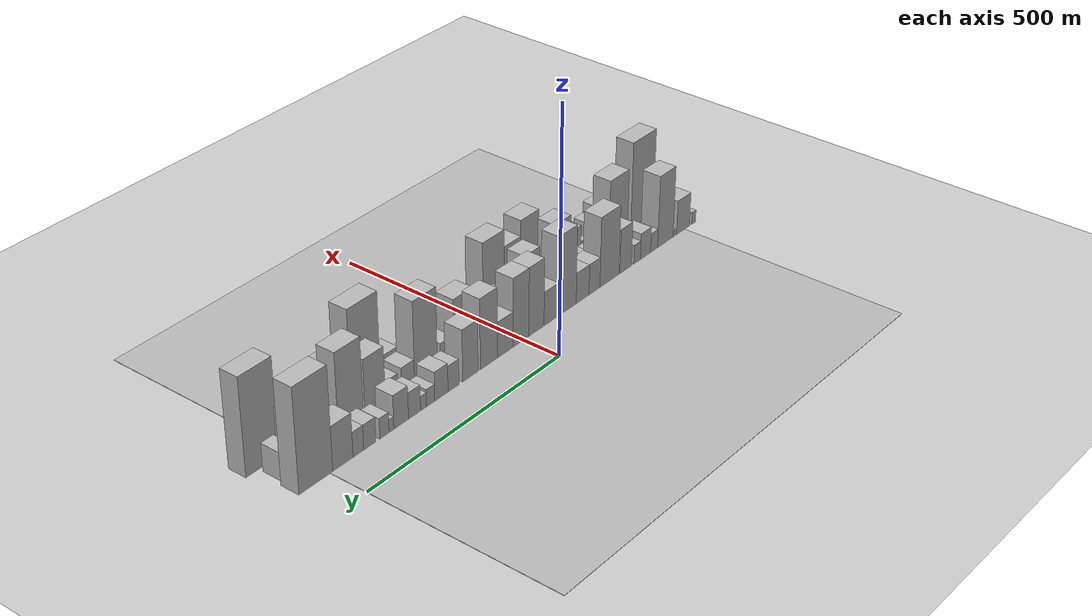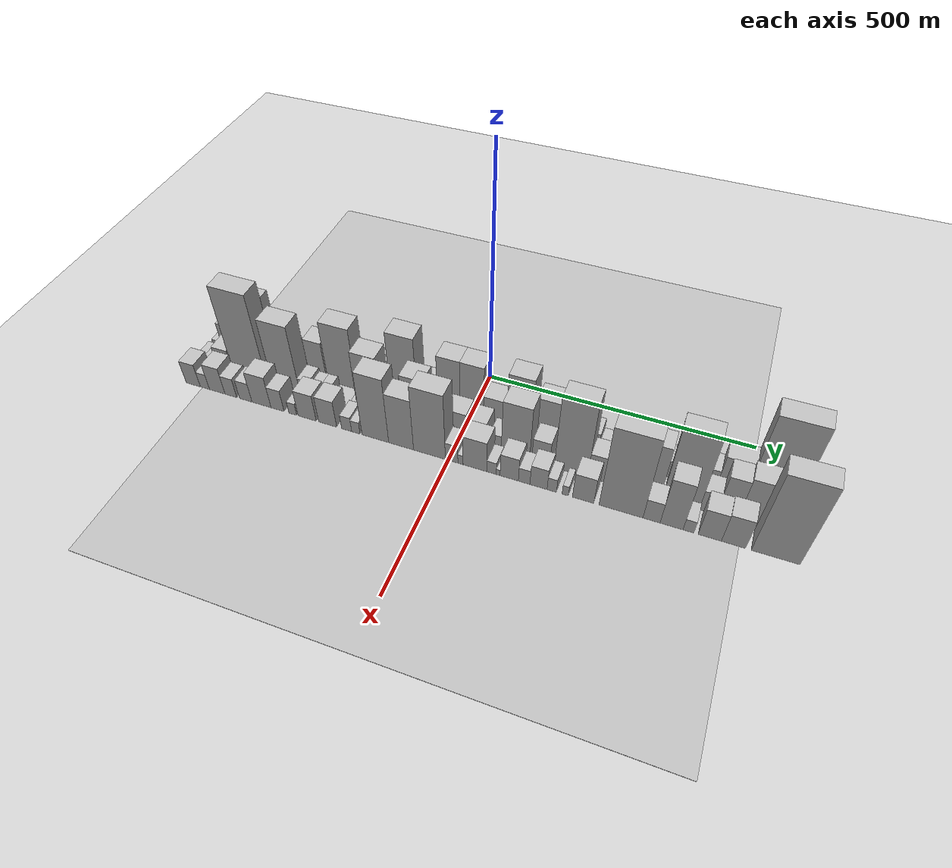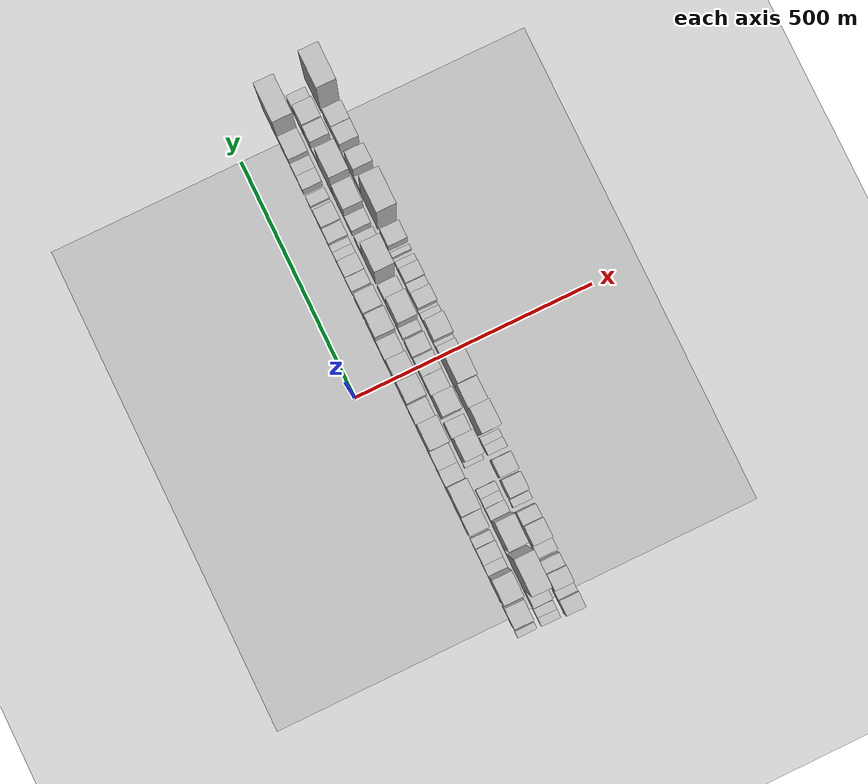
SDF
<?xml version="1.0" encoding="utf-8"?>

<sdf version="1.6">

   <world name="default">

      <gui fullscreen="0">

         <camera name="user_camera">

            <pose>-15 0 4.57585 0 0 0</pose>

            <view_controller>orbit</view_controller>

         </camera>

      </gui>

      <scene>

         <sky>

           <clouds>

             <speed>12</speed>

           </clouds>

         </sky>

         <ambient>0.4 0.4 0.4 1</ambient>

         <background>0.7 0.7 0.7 1</background>

         <shadows>1</shadows>

      </scene>

      <gravity>0 0 -9.8066</gravity>

      <magnetic_field>6e-06 2.3e-05 -4.2e-05</magnetic_field>

      <physics default="0" name="default_physics" type="ode">

         <ode>

            <solver>

               <type>quick</type>

               <iters>10</iters>

               <sor>1.0</sor>

               <use_dynamic_moi_rescaling>0</use_dynamic_moi_rescaling>

            </solver>

            <constraints>

               <cfm>0</cfm>

               <erp>0.2</erp>

               <contact_max_correcting_vel>100</contact_max_correcting_vel>

               <contact_surface_layer>0.001</contact_surface_layer>

            </constraints>

         </ode>

         <max_step_size>0.004</max_step_size>

         <real_time_factor>1</real_time_factor>

         <real_time_update_rate>250</real_time_update_rate>

      </physics>

      <light name="sun" type="directional">

         <cast_shadows>1</cast_shadows>

         <pose>0 0 10 0 0 0</pose>

         <diffuse>0.8 0.8 0.8 1</diffuse>

         <specular>0.2 0.2 0.2 1</specular>

         <attenuation>

            <range>1000</range>

            <constant>0.9</constant>

            <linear>0.01</linear>

            <quadratic>0.001</quadratic>

         </attenuation>

         <direction>-0.5 0.1 -0.9</direction>

      </light>

      <include>

         <name>ground_plane_1</name>

         <uri>model://HANNAS_ground_plane</uri>

         <pose>0 0 0  0 0 0</pose>

      </include>

      <include>

         <name>ground_plane_2</name>

         <uri>model://HANNAS_ground_plane</uri>

         <pose>100 0 0  0 0 0</pose>

      </include>

      <model name="building_1">

         <static>1</static>

         <pose frame="">100.0000 -529.4217 0 0.000000 0.000000 0.000000</pose>

         <link name="link">

            <pose frame="">0 0 13.50 0 0 0</pose>

            <collision name="collision">

               <geometry>

                  <box>

                     <size>40.0000 13.1565 27.0000</size>

                  </box>

               </geometry>

               <max_contacts>10</max_contacts>

               <surface>

                  <contact>

                     <ode/>

                  </contact>

                  <bounce/>

                  <friction>

                     <torsional>

                        <ode/>

                     </torsional>

                     <ode/>

                  </friction>

               </surface>

            </collision>

            <visual name="visual">

               <cast_shadows>0</cast_shadows>

               <geometry>

                  <box>

                     <size>40.0000 13.1565 27.0000</size>

                  </box>

               </geometry>

               <material>

                  <script>

                     <uri>model://HANNAS_wall/materials/scripts</uri>

                     <uri>model://HANNAS_wall/materials/textures</uri>

                     <name>vrc/HANNAS_wall</name>

                  </script>

               </material>

            </visual>

            <self_collide>0</self_collide>

            <enable_wind>0</enable_wind>

            <kinematic>0</kinematic>

         </link>

      </model>

      <model name="building_2">

         <static>1</static>

         <pose frame="">100.0000 -493.3523 0 0.000000 0.000000 0.000000</pose>

         <link name="link">

            <pose frame="">0 0 37.50 0 0 0</pose>

            <collision name="collision">

               <geometry>

                  <box>

                     <size>40.0000 42.9823 75.0000</size>

                  </box>

               </geometry>

               <max_contacts>10</max_contacts>

               <surface>

                  <contact>

                     <ode/>

                  </contact>

                  <bounce/>

                  <friction>

                     <torsional>

                        <ode/>

                     </torsional>

                     <ode/>

                  </friction>

               </surface>

            </collision>

            <visual name="visual">

               <cast_shadows>0</cast_shadows>

               <geometry>

                  <box>

                     <size>40.0000 42.9823 75.0000</size>

                  </box>

               </geometry>

               <material>

                  <script>

                     <uri>model://HANNAS_wall/materials/scripts</uri>

                     <uri>model://HANNAS_wall/materials/textures</uri>

                     <name>vrc/HANNAS_wall</name>

                  </script>

               </material>

            </visual>

            <self_collide>0</self_collide>

            <enable_wind>0</enable_wind>

            <kinematic>0</kinematic>

         </link>

      </model>

      <model name="building_3">

         <static>1</static>

         <pose frame="">100.0000 -462.7015 0 0.000000 0.000000 0.000000</pose>

         <link name="link">

            <pose frame="">0 0 7.50 0 0 0</pose>

            <collision name="collision">

               <geometry>

                  <box>

                     <size>40.0000 6.3195 15.0000</size>

                  </box>

               </geometry>

               <max_contacts>10</max_contacts>

               <surface>

                  <contact>

                     <ode/>

                  </contact>

                  <bounce/>

                  <friction>

                     <torsional>

                        <ode/>

                     </torsional>

                     <ode/>

                  </friction>

               </surface>

            </collision>

            <visual name="visual">

               <cast_shadows>0</cast_shadows>

               <geometry>

                  <box>

                     <size>40.0000 6.3195 15.0000</size>

                  </box>

               </geometry>

               <material>

                  <script>

                     <uri>model://HANNAS_wall/materials/scripts</uri>

                     <uri>model://HANNAS_wall/materials/textures</uri>

                     <name>vrc/HANNAS_wall</name>

                  </script>

               </material>

            </visual>

            <self_collide>0</self_collide>

            <enable_wind>0</enable_wind>

            <kinematic>0</kinematic>

         </link>

      </model>

      <model name="building_4">

         <static>1</static>

         <pose frame="">100.0000 -434.2183 0 0.000000 0.000000 0.000000</pose>

         <link name="link">

            <pose frame="">0 0 78.00 0 0 0</pose>

            <collision name="collision">

               <geometry>

                  <box>

                     <size>40.0000 50.6469 156.0000</size>

                  </box>

               </geometry>

               <max_contacts>10</max_contacts>

               <surface>

                  <contact>

                     <ode/>

                  </contact>

                  <bounce/>

                  <friction>

                     <torsional>

                        <ode/>

                     </torsional>

                     <ode/>

                  </friction>

               </surface>

            </collision>

            <visual name="visual">

               <cast_shadows>0</cast_shadows>

               <geometry>

                  <box>

                     <size>40.0000 50.6469 156.0000</size>

                  </box>

               </geometry>

               <material>

                  <script>

                     <uri>model://HANNAS_wall/materials/scripts</uri>

                     <uri>model://HANNAS_wall/materials/textures</uri>

                     <name>vrc/HANNAS_wall</name>

                  </script>

               </material>

            </visual>

            <self_collide>0</self_collide>

            <enable_wind>0</enable_wind>

            <kinematic>0</kinematic>

         </link>

      </model>

      <model name="building_5">

         <static>1</static>

         <pose frame="">100.0000 -397.5748 0 0.000000 0.000000 0.000000</pose>

         <link name="link">

            <pose frame="">0 0 21.00 0 0 0</pose>

            <collision name="collision">

               <geometry>

                  <box>

                     <size>40.0000 22.6401 42.0000</size>

                  </box>

               </geometry>

               <max_contacts>10</max_contacts>

               <surface>

                  <contact>

                     <ode/>

                  </contact>

                  <bounce/>

                  <friction>

                     <torsional>

                        <ode/>

                     </torsional>

                     <ode/>

                  </friction>

               </surface>

            </collision>

            <visual name="visual">

               <cast_shadows>0</cast_shadows>

               <geometry>

                  <box>

                     <size>40.0000 22.6401 42.0000</size>

                  </box>

               </geometry>

               <material>

                  <script>

                     <uri>model://HANNAS_wall/materials/scripts</uri>

                     <uri>model://HANNAS_wall/materials/textures</uri>

                     <name>vrc/HANNAS_wall</name>

                  </script>

               </material>

            </visual>

            <self_collide>0</self_collide>

            <enable_wind>0</enable_wind>

            <kinematic>0</kinematic>

         </link>

      </model>

      <model name="building_6">

         <static>1</static>

         <pose frame="">100.0000 -369.7955 0 0.000000 0.000000 0.000000</pose>

         <link name="link">

            <pose frame="">0 0 28.50 0 0 0</pose>

            <collision name="collision">

               <geometry>

                  <box>

                     <size>40.0000 32.9186 57.0000</size>

                  </box>

               </geometry>

               <max_contacts>10</max_contacts>

               <surface>

                  <contact>

                     <ode/>

                  </contact>

                  <bounce/>

                  <friction>

                     <torsional>

                        <ode/>

                     </torsional>

                     <ode/>

                  </friction>

               </surface>

            </collision>

            <visual name="visual">

               <cast_shadows>0</cast_shadows>

               <geometry>

                  <box>

                     <size>40.0000 32.9186 57.0000</size>

                  </box>

               </geometry>

               <material>

                  <script>

                     <uri>model://HANNAS_wall/materials/scripts</uri>

                     <uri>model://HANNAS_wall/materials/textures</uri>

                     <name>vrc/HANNAS_wall</name>

                  </script>

               </material>

            </visual>

            <self_collide>0</self_collide>

            <enable_wind>0</enable_wind>

            <kinematic>0</kinematic>

         </link>

      </model>

      <model name="building_7">

         <static>1</static>

         <pose frame="">100.0000 -342.6169 0 0.000000 0.000000 0.000000</pose>

         <link name="link">

            <pose frame="">0 0 21.00 0 0 0</pose>

            <collision name="collision">

               <geometry>

                  <box>

                     <size>40.0000 21.4385 42.0000</size>

                  </box>

               </geometry>

               <max_contacts>10</max_contacts>

               <surface>

                  <contact>

                     <ode/>

                  </contact>

                  <bounce/>

                  <friction>

                     <torsional>

                        <ode/>

                     </torsional>

                     <ode/>

                  </friction>

               </surface>

            </collision>

            <visual name="visual">

               <cast_shadows>0</cast_shadows>

               <geometry>

                  <box>

                     <size>40.0000 21.4385 42.0000</size>

                  </box>

               </geometry>

               <material>

                  <script>

                     <uri>model://HANNAS_wall/materials/scripts</uri>

                     <uri>model://HANNAS_wall/materials/textures</uri>

                     <name>vrc/HANNAS_wall</name>

                  </script>

               </material>

            </visual>

            <self_collide>0</self_collide>

            <enable_wind>0</enable_wind>

            <kinematic>0</kinematic>

         </link>

      </model>

      <model name="building_8">

         <static>1</static>

         <pose frame="">100.0000 -306.4331 0 0.000000 0.000000 0.000000</pose>

         <link name="link">

            <pose frame="">0 0 48.00 0 0 0</pose>

            <collision name="collision">

               <geometry>

                  <box>

                     <size>40.0000 36.9291 96.0000</size>

                  </box>

               </geometry>

               <max_contacts>10</max_contacts>

               <surface>

                  <contact>

                     <ode/>

                  </contact>

                  <bounce/>

                  <friction>

                     <torsional>

                        <ode/>

                     </torsional>

                     <ode/>

                  </friction>

               </surface>

            </collision>

            <visual name="visual">

               <cast_shadows>0</cast_shadows>

               <geometry>

                  <box>

                     <size>40.0000 36.9291 96.0000</size>

                  </box>

               </geometry>

               <material>

                  <script>

                     <uri>model://HANNAS_wall/materials/scripts</uri>

                     <uri>model://HANNAS_wall/materials/textures</uri>

                     <name>vrc/HANNAS_wall</name>

                  </script>

               </material>

            </visual>

            <self_collide>0</self_collide>

            <enable_wind>0</enable_wind>

            <kinematic>0</kinematic>

         </link>

      </model>

      <model name="building_9">

         <static>1</static>

         <pose frame="">100.0000 -255.4994 0 0.000000 0.000000 0.000000</pose>

         <link name="link">

            <pose frame="">0 0 75.00 0 0 0</pose>

            <collision name="collision">

               <geometry>

                  <box>

                     <size>40.0000 58.9382 150.0000</size>

                  </box>

               </geometry>

               <max_contacts>10</max_contacts>

               <surface>

                  <contact>

                     <ode/>

                  </contact>

                  <bounce/>

                  <friction>

                     <torsional>

                        <ode/>

                     </torsional>

                     <ode/>

                  </friction>

               </surface>

            </collision>

            <visual name="visual">

               <cast_shadows>0</cast_shadows>

               <geometry>

                  <box>

                     <size>40.0000 58.9382 150.0000</size>

                  </box>

               </geometry>

               <material>

                  <script>

                     <uri>model://HANNAS_wall/materials/scripts</uri>

                     <uri>model://HANNAS_wall/materials/textures</uri>

                     <name>vrc/HANNAS_wall</name>

                  </script>

               </material>

            </visual>

            <self_collide>0</self_collide>

            <enable_wind>0</enable_wind>

            <kinematic>0</kinematic>

         </link>

      </model>

      <model name="building_10">

         <static>1</static>

         <pose frame="">100.0000 -209.4669 0 0.000000 0.000000 0.000000</pose>

         <link name="link">

            <pose frame="">0 0 33.00 0 0 0</pose>

            <collision name="collision">

               <geometry>

                  <box>

                     <size>40.0000 33.1269 66.0000</size>

                  </box>

               </geometry>

               <max_contacts>10</max_contacts>

               <surface>

                  <contact>

                     <ode/>

                  </contact>

                  <bounce/>

                  <friction>

                     <torsional>

                        <ode/>

                     </torsional>

                     <ode/>

                  </friction>

               </surface>

            </collision>

            <visual name="visual">

               <cast_shadows>0</cast_shadows>

               <geometry>

                  <box>

                     <size>40.0000 33.1269 66.0000</size>

                  </box>

               </geometry>

               <material>

                  <script>

                     <uri>model://HANNAS_wall/materials/scripts</uri>

                     <uri>model://HANNAS_wall/materials/textures</uri>

                     <name>vrc/HANNAS_wall</name>

                  </script>

               </material>

            </visual>

            <self_collide>0</self_collide>

            <enable_wind>0</enable_wind>

            <kinematic>0</kinematic>

         </link>

      </model>

      <model name="building_11">

         <static>1</static>

         <pose frame="">100.0000 -173.3892 0 0.000000 0.000000 0.000000</pose>

         <link name="link">

            <pose frame="">0 0 33.00 0 0 0</pose>

            <collision name="collision">

               <geometry>

                  <box>

                     <size>40.0000 39.0284 66.0000</size>

                  </box>

               </geometry>

               <max_contacts>10</max_contacts>

               <surface>

                  <contact>

                     <ode/>

                  </contact>

                  <bounce/>

                  <friction>

                     <torsional>

                        <ode/>

                     </torsional>

                     <ode/>

                  </friction>

               </surface>

            </collision>

            <visual name="visual">

               <cast_shadows>0</cast_shadows>

               <geometry>

                  <box>

                     <size>40.0000 39.0284 66.0000</size>

                  </box>

               </geometry>

               <material>

                  <script>

                     <uri>model://HANNAS_wall/materials/scripts</uri>

                     <uri>model://HANNAS_wall/materials/textures</uri>

                     <name>vrc/HANNAS_wall</name>

                  </script>

               </material>

            </visual>

            <self_collide>0</self_collide>

            <enable_wind>0</enable_wind>

            <kinematic>0</kinematic>

         </link>

      </model>

      <model name="building_12">

         <static>1</static>

         <pose frame="">100.0000 -127.2653 0 0.000000 0.000000 0.000000</pose>

         <link name="link">

            <pose frame="">0 0 84.00 0 0 0</pose>

            <collision name="collision">

               <geometry>

                  <box>

                     <size>40.0000 53.2196 168.0000</size>

                  </box>

               </geometry>

               <max_contacts>10</max_contacts>

               <surface>

                  <contact>

                     <ode/>

                  </contact>

                  <bounce/>

                  <friction>

                     <torsional>

                        <ode/>

                     </torsional>

                     <ode/>

                  </friction>

               </surface>

            </collision>

            <visual name="visual">

               <cast_shadows>0</cast_shadows>

               <geometry>

                  <box>

                     <size>40.0000 53.2196 168.0000</size>

                  </box>

               </geometry>

               <material>

                  <script>

                     <uri>model://HANNAS_wall/materials/scripts</uri>

                     <uri>model://HANNAS_wall/materials/textures</uri>

                     <name>vrc/HANNAS_wall</name>

                  </script>

               </material>

            </visual>

            <self_collide>0</self_collide>

            <enable_wind>0</enable_wind>

            <kinematic>0</kinematic>

         </link>

      </model>

      <model name="building_13">

         <static>1</static>

         <pose frame="">100.0000 -79.9230 0 0.000000 0.000000 0.000000</pose>

         <link name="link">

            <pose frame="">0 0 36.00 0 0 0</pose>

            <collision name="collision">

               <geometry>

                  <box>

                     <size>40.0000 41.4650 72.0000</size>

                  </box>

               </geometry>

               <max_contacts>10</max_contacts>

               <surface>

                  <contact>

                     <ode/>

                  </contact>

                  <bounce/>

                  <friction>

                     <torsional>

                        <ode/>

                     </torsional>

                     <ode/>

                  </friction>

               </surface>

            </collision>

            <visual name="visual">

               <cast_shadows>0</cast_shadows>

               <geometry>

                  <box>

                     <size>40.0000 41.4650 72.0000</size>

                  </box>

               </geometry>

               <material>

                  <script>

                     <uri>model://HANNAS_wall/materials/scripts</uri>

                     <uri>model://HANNAS_wall/materials/textures</uri>

                     <name>vrc/HANNAS_wall</name>

                  </script>

               </material>

            </visual>

            <self_collide>0</self_collide>

            <enable_wind>0</enable_wind>

            <kinematic>0</kinematic>

         </link>

      </model>

      <model name="building_14">

         <static>1</static>

         <pose frame="">100.0000 -37.3843 0 0.000000 0.000000 0.000000</pose>

         <link name="link">

            <pose frame="">0 0 72.00 0 0 0</pose>

            <collision name="collision">

               <geometry>

                  <box>

                     <size>40.0000 43.6123 144.0000</size>

                  </box>

               </geometry>

               <max_contacts>10</max_contacts>

               <surface>

                  <contact>

                     <ode/>

                  </contact>

                  <bounce/>

                  <friction>

                     <torsional>

                        <ode/>

                     </torsional>

                     <ode/>

                  </friction>

               </surface>

            </collision>

            <visual name="visual">

               <cast_shadows>0</cast_shadows>

               <geometry>

                  <box>

                     <size>40.0000 43.6123 144.0000</size>

                  </box>

               </geometry>

               <material>

                  <script>

                     <uri>model://HANNAS_wall/materials/scripts</uri>

                     <uri>model://HANNAS_wall/materials/textures</uri>

                     <name>vrc/HANNAS_wall</name>

                  </script>

               </material>

            </visual>

            <self_collide>0</self_collide>

            <enable_wind>0</enable_wind>

            <kinematic>0</kinematic>

         </link>

      </model>

      <model name="building_15">

         <static>1</static>

         <pose frame="">100.0000 6.9200 0 0.000000 0.000000 0.000000</pose>

         <link name="link">

            <pose frame="">0 0 72.00 0 0 0</pose>

            <collision name="collision">

               <geometry>

                  <box>

                     <size>40.0000 44.9962 144.0000</size>

                  </box>

               </geometry>

               <max_contacts>10</max_contacts>

               <surface>

                  <contact>

                     <ode/>

                  </contact>

                  <bounce/>

                  <friction>

                     <torsional>

                        <ode/>

                     </torsional>

                     <ode/>

                  </friction>

               </surface>

            </collision>

            <visual name="visual">

               <cast_shadows>0</cast_shadows>

               <geometry>

                  <box>

                     <size>40.0000 44.9962 144.0000</size>

                  </box>

               </geometry>

               <material>

                  <script>

                     <uri>model://HANNAS_wall/materials/scripts</uri>

                     <uri>model://HANNAS_wall/materials/textures</uri>

                     <name>vrc/HANNAS_wall</name>

                  </script>

               </material>

            </visual>

            <self_collide>0</self_collide>

            <enable_wind>0</enable_wind>

            <kinematic>0</kinematic>

         </link>

      </model>

      <model name="building_16">

         <static>1</static>

         <pose frame="">100.0000 51.2852 0 0.000000 0.000000 0.000000</pose>

         <link name="link">

            <pose frame="">0 0 37.50 0 0 0</pose>

            <collision name="collision">

               <geometry>

                  <box>

                     <size>40.0000 43.7342 75.0000</size>

                  </box>

               </geometry>

               <max_contacts>10</max_contacts>

               <surface>

                  <contact>

                     <ode/>

                  </contact>

                  <bounce/>

                  <friction>

                     <torsional>

                        <ode/>

                     </torsional>

                     <ode/>

                  </friction>

               </surface>

            </collision>

            <visual name="visual">

               <cast_shadows>0</cast_shadows>

               <geometry>

                  <box>

                     <size>40.0000 43.7342 75.0000</size>

                  </box>

               </geometry>

               <material>

                  <script>

                     <uri>model://HANNAS_wall/materials/scripts</uri>

                     <uri>model://HANNAS_wall/materials/textures</uri>

                     <name>vrc/HANNAS_wall</name>

                  </script>

               </material>

            </visual>

            <self_collide>0</self_collide>

            <enable_wind>0</enable_wind>

            <kinematic>0</kinematic>

         </link>

      </model>

      <model name="building_17">

         <static>1</static>

         <pose frame="">100.0000 96.6755 0 0.000000 0.000000 0.000000</pose>

         <link name="link">

            <pose frame="">0 0 73.50 0 0 0</pose>

            <collision name="collision">

               <geometry>

                  <box>

                     <size>40.0000 47.0465 147.0000</size>

                  </box>

               </geometry>

               <max_contacts>10</max_contacts>

               <surface>

                  <contact>

                     <ode/>

                  </contact>

                  <bounce/>

                  <friction>

                     <torsional>

                        <ode/>

                     </torsional>

                     <ode/>

                  </friction>

               </surface>

            </collision>

            <visual name="visual">

               <cast_shadows>0</cast_shadows>

               <geometry>

                  <box>

                     <size>40.0000 47.0465 147.0000</size>

                  </box>

               </geometry>

               <material>

                  <script>

                     <uri>model://HANNAS_wall/materials/scripts</uri>

                     <uri>model://HANNAS_wall/materials/textures</uri>

                     <name>vrc/HANNAS_wall</name>

                  </script>

               </material>

            </visual>

            <self_collide>0</self_collide>

            <enable_wind>0</enable_wind>

            <kinematic>0</kinematic>

         </link>

      </model>

      <model name="building_18">

         <static>1</static>

         <pose frame="">100.0000 146.9544 0 0.000000 0.000000 0.000000</pose>

         <link name="link">

            <pose frame="">0 0 54.00 0 0 0</pose>

            <collision name="collision">

               <geometry>

                  <box>

                     <size>40.0000 41.5112 108.0000</size>

                  </box>

               </geometry>

               <max_contacts>10</max_contacts>

               <surface>

                  <contact>

                     <ode/>

                  </contact>

                  <bounce/>

                  <friction>

                     <torsional>

                        <ode/>

                     </torsional>

                     <ode/>

                  </friction>

               </surface>

            </collision>

            <visual name="visual">

               <cast_shadows>0</cast_shadows>

               <geometry>

                  <box>

                     <size>40.0000 41.5112 108.0000</size>

                  </box>

               </geometry>

               <material>

                  <script>

                     <uri>model://HANNAS_wall/materials/scripts</uri>

                     <uri>model://HANNAS_wall/materials/textures</uri>

                     <name>vrc/HANNAS_wall</name>

                  </script>

               </material>

            </visual>

            <self_collide>0</self_collide>

            <enable_wind>0</enable_wind>

            <kinematic>0</kinematic>

         </link>

      </model>

      <model name="building_19">

         <static>1</static>

         <pose frame="">100.0000 192.1107 0 0.000000 0.000000 0.000000</pose>

         <link name="link">

            <pose frame="">0 0 27.00 0 0 0</pose>

            <collision name="collision">

               <geometry>

                  <box>

                     <size>40.0000 28.8016 54.0000</size>

                  </box>

               </geometry>

               <max_contacts>10</max_contacts>

               <surface>

                  <contact>

                     <ode/>

                  </contact>

                  <bounce/>

                  <friction>

                     <torsional>

                        <ode/>

                     </torsional>

                     <ode/>

                  </friction>

               </surface>

            </collision>

            <visual name="visual">

               <cast_shadows>0</cast_shadows>

               <geometry>

                  <box>

                     <size>40.0000 28.8016 54.0000</size>

                  </box>

               </geometry>

               <material>

                  <script>

                     <uri>model://HANNAS_wall/materials/scripts</uri>

                     <uri>model://HANNAS_wall/materials/textures</uri>

                     <name>vrc/HANNAS_wall</name>

                  </script>

               </material>

            </visual>

            <self_collide>0</self_collide>

            <enable_wind>0</enable_wind>

            <kinematic>0</kinematic>

         </link>

      </model>

      <model name="building_20">

         <static>1</static>

         <pose frame="">100.0000 223.8757 0 0.000000 0.000000 0.000000</pose>

         <link name="link">

            <pose frame="">0 0 30.00 0 0 0</pose>

            <collision name="collision">

               <geometry>

                  <box>

                     <size>40.0000 34.7284 60.0000</size>

                  </box>

               </geometry>

               <max_contacts>10</max_contacts>

               <surface>

                  <contact>

                     <ode/>

                  </contact>

                  <bounce/>

                  <friction>

                     <torsional>

                        <ode/>

                     </torsional>

                     <ode/>

                  </friction>

               </surface>

            </collision>

            <visual name="visual">

               <cast_shadows>0</cast_shadows>

               <geometry>

                  <box>

                     <size>40.0000 34.7284 60.0000</size>

                  </box>

               </geometry>

               <material>

                  <script>

                     <uri>model://HANNAS_wall/materials/scripts</uri>

                     <uri>model://HANNAS_wall/materials/textures</uri>

                     <name>vrc/HANNAS_wall</name>

                  </script>

               </material>

            </visual>

            <self_collide>0</self_collide>

            <enable_wind>0</enable_wind>

            <kinematic>0</kinematic>

         </link>

      </model>

      <model name="building_21">

         <static>1</static>

         <pose frame="">100.0000 251.9050 0 0.000000 0.000000 0.000000</pose>

         <link name="link">

            <pose frame="">0 0 18.00 0 0 0</pose>

            <collision name="collision">

               <geometry>

                  <box>

                     <size>40.0000 21.3302 36.0000</size>

                  </box>

               </geometry>

               <max_contacts>10</max_contacts>

               <surface>

                  <contact>

                     <ode/>

                  </contact>

                  <bounce/>

                  <friction>

                     <torsional>

                        <ode/>

                     </torsional>

                     <ode/>

                  </friction>

               </surface>

            </collision>

            <visual name="visual">

               <cast_shadows>0</cast_shadows>

               <geometry>

                  <box>

                     <size>40.0000 21.3302 36.0000</size>

                  </box>

               </geometry>

               <material>

                  <script>

                     <uri>model://HANNAS_wall/materials/scripts</uri>

                     <uri>model://HANNAS_wall/materials/textures</uri>

                     <name>vrc/HANNAS_wall</name>

                  </script>

               </material>

            </visual>

            <self_collide>0</self_collide>

            <enable_wind>0</enable_wind>

            <kinematic>0</kinematic>

         </link>

      </model>

      <model name="building_22">

         <static>1</static>

         <pose frame="">100.0000 270.2746 0 0.000000 0.000000 0.000000</pose>

         <link name="link">

            <pose frame="">0 0 15.00 0 0 0</pose>

            <collision name="collision">

               <geometry>

                  <box>

                     <size>40.0000 15.4090 30.0000</size>

                  </box>

               </geometry>

               <max_contacts>10</max_contacts>

               <surface>

                  <contact>

                     <ode/>

                  </contact>

                  <bounce/>

                  <friction>

                     <torsional>

                        <ode/>

                     </torsional>

                     <ode/>

                  </friction>

               </surface>

            </collision>

            <visual name="visual">

               <cast_shadows>0</cast_shadows>

               <geometry>

                  <box>

                     <size>40.0000 15.4090 30.0000</size>

                  </box>

               </geometry>

               <material>

                  <script>

                     <uri>model://HANNAS_wall/materials/scripts</uri>

                     <uri>model://HANNAS_wall/materials/textures</uri>

                     <name>vrc/HANNAS_wall</name>

                  </script>

               </material>

            </visual>

            <self_collide>0</self_collide>

            <enable_wind>0</enable_wind>

            <kinematic>0</kinematic>

         </link>

      </model>

      <model name="building_23">

         <static>1</static>

         <pose frame="">100.0000 293.4356 0 0.000000 0.000000 0.000000</pose>

         <link name="link">

            <pose frame="">0 0 27.00 0 0 0</pose>

            <collision name="collision">

               <geometry>

                  <box>

                     <size>40.0000 30.9131 54.0000</size>

                  </box>

               </geometry>

               <max_contacts>10</max_contacts>

               <surface>

                  <contact>

                     <ode/>

                  </contact>

                  <bounce/>

                  <friction>

                     <torsional>

                        <ode/>

                     </torsional>

                     <ode/>

                  </friction>

               </surface>

            </collision>

            <visual name="visual">

               <cast_shadows>0</cast_shadows>

               <geometry>

                  <box>

                     <size>40.0000 30.9131 54.0000</size>

                  </box>

               </geometry>

               <material>

                  <script>

                     <uri>model://HANNAS_wall/materials/scripts</uri>

                     <uri>model://HANNAS_wall/materials/textures</uri>

                     <name>vrc/HANNAS_wall</name>

                  </script>

               </material>

            </visual>

            <self_collide>0</self_collide>

            <enable_wind>0</enable_wind>

            <kinematic>0</kinematic>

         </link>

      </model>

      <model name="building_24">

         <static>1</static>

         <pose frame="">100.0000 327.2846 0 0.000000 0.000000 0.000000</pose>

         <link name="link">

            <pose frame="">0 0 34.50 0 0 0</pose>

            <collision name="collision">

               <geometry>

                  <box>

                     <size>40.0000 36.7847 69.0000</size>

                  </box>

               </geometry>

               <max_contacts>10</max_contacts>

               <surface>

                  <contact>

                     <ode/>

                  </contact>

                  <bounce/>

                  <friction>

                     <torsional>

                        <ode/>

                     </torsional>

                     <ode/>

                  </friction>

               </surface>

            </collision>

            <visual name="visual">

               <cast_shadows>0</cast_shadows>

               <geometry>

                  <box>

                     <size>40.0000 36.7847 69.0000</size>

                  </box>

               </geometry>

               <material>

                  <script>

                     <uri>model://HANNAS_wall/materials/scripts</uri>

                     <uri>model://HANNAS_wall/materials/textures</uri>

                     <name>vrc/HANNAS_wall</name>

                  </script>

               </material>

            </visual>

            <self_collide>0</self_collide>

            <enable_wind>0</enable_wind>

            <kinematic>0</kinematic>

         </link>

      </model>

      <model name="building_25">

         <static>1</static>

         <pose frame="">100.0000 351.6811 0 0.000000 0.000000 0.000000</pose>

         <link name="link">

            <pose frame="">0 0 13.50 0 0 0</pose>

            <collision name="collision">

               <geometry>

                  <box>

                     <size>40.0000 12.0084 27.0000</size>

                  </box>

               </geometry>

               <max_contacts>10</max_contacts>

               <surface>

                  <contact>

                     <ode/>

                  </contact>

                  <bounce/>

                  <friction>

                     <torsional>

                        <ode/>

                     </torsional>

                     <ode/>

                  </friction>

               </surface>

            </collision>

            <visual name="visual">

               <cast_shadows>0</cast_shadows>

               <geometry>

                  <box>

                     <size>40.0000 12.0084 27.0000</size>

                  </box>

               </geometry>

               <material>

                  <script>

                     <uri>model://HANNAS_wall/materials/scripts</uri>

                     <uri>model://HANNAS_wall/materials/textures</uri>

                     <name>vrc/HANNAS_wall</name>

                  </script>

               </material>

            </visual>

            <self_collide>0</self_collide>

            <enable_wind>0</enable_wind>

            <kinematic>0</kinematic>

         </link>

      </model>

      <model name="building_26">

         <static>1</static>

         <pose frame="">100.0000 369.1910 0 0.000000 0.000000 0.000000</pose>

         <link name="link">

            <pose frame="">0 0 21.00 0 0 0</pose>

            <collision name="collision">

               <geometry>

                  <box>

                     <size>40.0000 23.0114 42.0000</size>

                  </box>

               </geometry>

               <max_contacts>10</max_contacts>

               <surface>

                  <contact>

                     <ode/>

                  </contact>

                  <bounce/>

                  <friction>

                     <torsional>

                        <ode/>

                     </torsional>

                     <ode/>

                  </friction>

               </surface>

            </collision>

            <visual name="visual">

               <cast_shadows>0</cast_shadows>

               <geometry>

                  <box>

                     <size>40.0000 23.0114 42.0000</size>

                  </box>

               </geometry>

               <material>

                  <script>

                     <uri>model://HANNAS_wall/materials/scripts</uri>

                     <uri>model://HANNAS_wall/materials/textures</uri>

                     <name>vrc/HANNAS_wall</name>

                  </script>

               </material>

            </visual>

            <self_collide>0</self_collide>

            <enable_wind>0</enable_wind>

            <kinematic>0</kinematic>

         </link>

      </model>

      <model name="building_27">

         <static>1</static>

         <pose frame="">100.0000 405.4047 0 0.000000 0.000000 0.000000</pose>

         <link name="link">

            <pose frame="">0 0 25.50 0 0 0</pose>

            <collision name="collision">

               <geometry>

                  <box>

                     <size>40.0000 29.4160 51.0000</size>

                  </box>

               </geometry>

               <max_contacts>10</max_contacts>

               <surface>

                  <contact>

                     <ode/>

                  </contact>

                  <bounce/>

                  <friction>

                     <torsional>

                        <ode/>

                     </torsional>

                     <ode/>

                  </friction>

               </surface>

            </collision>

            <visual name="visual">

               <cast_shadows>0</cast_shadows>

               <geometry>

                  <box>

                     <size>40.0000 29.4160 51.0000</size>

                  </box>

               </geometry>

               <material>

                  <script>

                     <uri>model://HANNAS_wall/materials/scripts</uri>

                     <uri>model://HANNAS_wall/materials/textures</uri>

                     <name>vrc/HANNAS_wall</name>

                  </script>

               </material>

            </visual>

            <self_collide>0</self_collide>

            <enable_wind>0</enable_wind>

            <kinematic>0</kinematic>

         </link>

      </model>

      <model name="building_28">

         <static>1</static>

         <pose frame="">100.0000 433.1273 0 0.000000 0.000000 0.000000</pose>

         <link name="link">

            <pose frame="">0 0 25.50 0 0 0</pose>

            <collision name="collision">

               <geometry>

                  <box>

                     <size>40.0000 26.0293 51.0000</size>

                  </box>

               </geometry>

               <max_contacts>10</max_contacts>

               <surface>

                  <contact>

                     <ode/>

                  </contact>

                  <bounce/>

                  <friction>

                     <torsional>

                        <ode/>

                     </torsional>

                     <ode/>

                  </friction>

               </surface>

            </collision>

            <visual name="visual">

               <cast_shadows>0</cast_shadows>

               <geometry>

                  <box>

                     <size>40.0000 26.0293 51.0000</size>

                  </box>

               </geometry>

               <material>

                  <script>

                     <uri>model://HANNAS_wall/materials/scripts</uri>

                     <uri>model://HANNAS_wall/materials/textures</uri>

                     <name>vrc/HANNAS_wall</name>

                  </script>

               </material>

            </visual>

            <self_collide>0</self_collide>

            <enable_wind>0</enable_wind>

            <kinematic>0</kinematic>

         </link>

      </model>

      <model name="building_29">

         <static>1</static>

         <pose frame="">100.0000 470.3106 0 0.000000 0.000000 0.000000</pose>

         <link name="link">

            <pose frame="">0 0 45.00 0 0 0</pose>

            <collision name="collision">

               <geometry>

                  <box>

                     <size>40.0000 48.3374 90.0000</size>

                  </box>

               </geometry>

               <max_contacts>10</max_contacts>

               <surface>

                  <contact>

                     <ode/>

                  </contact>

                  <bounce/>

                  <friction>

                     <torsional>

                        <ode/>

                     </torsional>

                     <ode/>

                  </friction>

               </surface>

            </collision>

            <visual name="visual">

               <cast_shadows>0</cast_shadows>

               <geometry>

                  <box>

                     <size>40.0000 48.3374 90.0000</size>

                  </box>

               </geometry>

               <material>

                  <script>

                     <uri>model://HANNAS_wall/materials/scripts</uri>

                     <uri>model://HANNAS_wall/materials/textures</uri>

                     <name>vrc/HANNAS_wall</name>

                  </script>

               </material>

            </visual>

            <self_collide>0</self_collide>

            <enable_wind>0</enable_wind>

            <kinematic>0</kinematic>

         </link>

      </model>

      <model name="building_30">

         <static>1</static>

         <pose frame="">100.0000 533.9974 0 0.000000 0.000000 0.000000</pose>

         <link name="link">

            <pose frame="">0 0 105.00 0 0 0</pose>

            <collision name="collision">

               <geometry>

                  <box>

                     <size>40.0000 79.0361 210.0000</size>

                  </box>

               </geometry>

               <max_contacts>10</max_contacts>

               <surface>

                  <contact>

                     <ode/>

                  </contact>

                  <bounce/>

                  <friction>

                     <torsional>

                        <ode/>

                     </torsional>

                     <ode/>

                  </friction>

               </surface>

            </collision>

            <visual name="visual">

               <cast_shadows>0</cast_shadows>

               <geometry>

                  <box>

                     <size>40.0000 79.0361 210.0000</size>

                  </box>

               </geometry>

               <material>

                  <script>

                     <uri>model://HANNAS_wall/materials/scripts</uri>

                     <uri>model://HANNAS_wall/materials/textures</uri>

                     <name>vrc/HANNAS_wall</name>

                  </script>

               </material>

            </visual>

            <self_collide>0</self_collide>

            <enable_wind>0</enable_wind>

            <kinematic>0</kinematic>

         </link>

      </model>

      <model name="building_31">

         <static>1</static>

         <pose frame="">149.0000 -527.3067 0 0.000000 0.000000 0.000000</pose>

         <link name="link">

            <pose frame="">0 0 15.00 0 0 0</pose>

            <collision name="collision">

               <geometry>

                  <box>

                     <size>40.0000 17.3866 30.0000</size>

                  </box>

               </geometry>

               <max_contacts>10</max_contacts>

               <surface>

                  <contact>

                     <ode/>

                  </contact>

                  <bounce/>

                  <friction>

                     <torsional>

                        <ode/>

                     </torsional>

                     <ode/>

                  </friction>

               </surface>

            </collision>

            <visual name="visual">

               <cast_shadows>0</cast_shadows>

               <geometry>

                  <box>

                     <size>40.0000 17.3866 30.0000</size>

                  </box>

               </geometry>

               <material>

                  <script>

                     <uri>model://HANNAS_wall/materials/scripts</uri>

                     <uri>model://HANNAS_wall/materials/textures</uri>

                     <name>vrc/HANNAS_wall</name>

                  </script>

               </material>

            </visual>

            <self_collide>0</self_collide>

            <enable_wind>0</enable_wind>

            <kinematic>0</kinematic>

         </link>

      </model>

      <model name="building_32">

         <static>1</static>

         <pose frame="">149.0000 -509.4742 0 0.000000 0.000000 0.000000</pose>

         <link name="link">

            <pose frame="">0 0 16.50 0 0 0</pose>

            <collision name="collision">

               <geometry>

                  <box>

                     <size>40.0000 18.2785 33.0000</size>

                  </box>

               </geometry>

               <max_contacts>10</max_contacts>

               <surface>

                  <contact>

                     <ode/>

                  </contact>

                  <bounce/>

                  <friction>

                     <torsional>

                        <ode/>

                     </torsional>

                     <ode/>

                  </friction>

               </surface>

            </collision>

            <visual name="visual">

               <cast_shadows>0</cast_shadows>

               <geometry>

                  <box>

                     <size>40.0000 18.2785 33.0000</size>

                  </box>

               </geometry>

               <material>

                  <script>

                     <uri>model://HANNAS_wall/materials/scripts</uri>

                     <uri>model://HANNAS_wall/materials/textures</uri>

                     <name>vrc/HANNAS_wall</name>

                  </script>

               </material>

            </visual>

            <self_collide>0</self_collide>

            <enable_wind>0</enable_wind>

            <kinematic>0</kinematic>

         </link>

      </model>

      <model name="building_33">

         <static>1</static>

         <pose frame="">149.0000 -479.9805 0 0.000000 0.000000 0.000000</pose>

         <link name="link">

            <pose frame="">0 0 31.50 0 0 0</pose>

            <collision name="collision">

               <geometry>

                  <box>

                     <size>40.0000 32.7088 63.0000</size>

                  </box>

               </geometry>

               <max_contacts>10</max_contacts>

               <surface>

                  <contact>

                     <ode/>

                  </contact>

                  <bounce/>

                  <friction>

                     <torsional>

                        <ode/>

                     </torsional>

                     <ode/>

                  </friction>

               </surface>

            </collision>

            <visual name="visual">

               <cast_shadows>0</cast_shadows>

               <geometry>

                  <box>

                     <size>40.0000 32.7088 63.0000</size>

                  </box>

               </geometry>

               <material>

                  <script>

                     <uri>model://HANNAS_wall/materials/scripts</uri>

                     <uri>model://HANNAS_wall/materials/textures</uri>

                     <name>vrc/HANNAS_wall</name>

                  </script>

               </material>

            </visual>

            <self_collide>0</self_collide>

            <enable_wind>0</enable_wind>

            <kinematic>0</kinematic>

         </link>

      </model>

      <model name="building_34">

         <static>1</static>

         <pose frame="">149.0000 -424.2670 0 0.000000 0.000000 0.000000</pose>

         <link name="link">

            <pose frame="">0 0 109.50 0 0 0</pose>

            <collision name="collision">

               <geometry>

                  <box>

                     <size>40.0000 72.7183 219.0000</size>

                  </box>

               </geometry>

               <max_contacts>10</max_contacts>

               <surface>

                  <contact>

                     <ode/>

                  </contact>

                  <bounce/>

                  <friction>

                     <torsional>

                        <ode/>

                     </torsional>

                     <ode/>

                  </friction>

               </surface>

            </collision>

            <visual name="visual">

               <cast_shadows>0</cast_shadows>

               <geometry>

                  <box>

                     <size>40.0000 72.7183 219.0000</size>

                  </box>

               </geometry>

               <material>

                  <script>

                     <uri>model://HANNAS_wall/materials/scripts</uri>

                     <uri>model://HANNAS_wall/materials/textures</uri>

                     <name>vrc/HANNAS_wall</name>

                  </script>

               </material>

            </visual>

            <self_collide>0</self_collide>

            <enable_wind>0</enable_wind>

            <kinematic>0</kinematic>

         </link>

      </model>

      <model name="building_35">

         <static>1</static>

         <pose frame="">149.0000 -382.2110 0 0.000000 0.000000 0.000000</pose>

         <link name="link">

            <pose frame="">0 0 13.50 0 0 0</pose>

            <collision name="collision">

               <geometry>

                  <box>

                     <size>40.0000 11.3936 27.0000</size>

                  </box>

               </geometry>

               <max_contacts>10</max_contacts>

               <surface>

                  <contact>

                     <ode/>

                  </contact>

                  <bounce/>

                  <friction>

                     <torsional>

                        <ode/>

                     </torsional>

                     <ode/>

                  </friction>

               </surface>

            </collision>

            <visual name="visual">

               <cast_shadows>0</cast_shadows>

               <geometry>

                  <box>

                     <size>40.0000 11.3936 27.0000</size>

                  </box>

               </geometry>

               <material>

                  <script>

                     <uri>model://HANNAS_wall/materials/scripts</uri>

                     <uri>model://HANNAS_wall/materials/textures</uri>

                     <name>vrc/HANNAS_wall</name>

                  </script>

               </material>

            </visual>

            <self_collide>0</self_collide>

            <enable_wind>0</enable_wind>

            <kinematic>0</kinematic>

         </link>

      </model>

      <model name="building_36">

         <static>1</static>

         <pose frame="">149.0000 -347.4596 0 0.000000 0.000000 0.000000</pose>

         <link name="link">

            <pose frame="">0 0 84.00 0 0 0</pose>

            <collision name="collision">

               <geometry>

                  <box>

                     <size>40.0000 58.1094 168.0000</size>

                  </box>

               </geometry>

               <max_contacts>10</max_contacts>

               <surface>

                  <contact>

                     <ode/>

                  </contact>

                  <bounce/>

                  <friction>

                     <torsional>

                        <ode/>

                     </torsional>

                     <ode/>

                  </friction>

               </surface>

            </collision>

            <visual name="visual">

               <cast_shadows>0</cast_shadows>

               <geometry>

                  <box>

                     <size>40.0000 58.1094 168.0000</size>

                  </box>

               </geometry>

               <material>

                  <script>

                     <uri>model://HANNAS_wall/materials/scripts</uri>

                     <uri>model://HANNAS_wall/materials/textures</uri>

                     <name>vrc/HANNAS_wall</name>

                  </script>

               </material>

            </visual>

            <self_collide>0</self_collide>

            <enable_wind>0</enable_wind>

            <kinematic>0</kinematic>

         </link>

      </model>

      <model name="building_37">

         <static>1</static>

         <pose frame="">149.0000 -306.1658 0 0.000000 0.000000 0.000000</pose>

         <link name="link">

            <pose frame="">0 0 21.00 0 0 0</pose>

            <collision name="collision">

               <geometry>

                  <box>

                     <size>40.0000 24.4781 42.0000</size>

                  </box>

               </geometry>

               <max_contacts>10</max_contacts>

               <surface>

                  <contact>

                     <ode/>

                  </contact>

                  <bounce/>

                  <friction>

                     <torsional>

                        <ode/>

                     </torsional>

                     <ode/>

                  </friction>

               </surface>

            </collision>

            <visual name="visual">

               <cast_shadows>0</cast_shadows>

               <geometry>

                  <box>

                     <size>40.0000 24.4781 42.0000</size>

                  </box>

               </geometry>

               <material>

                  <script>

                     <uri>model://HANNAS_wall/materials/scripts</uri>

                     <uri>model://HANNAS_wall/materials/textures</uri>

                     <name>vrc/HANNAS_wall</name>

                  </script>

               </material>

            </visual>

            <self_collide>0</self_collide>

            <enable_wind>0</enable_wind>

            <kinematic>0</kinematic>

         </link>

      </model>

      <model name="building_38">

         <static>1</static>

         <pose frame="">149.0000 -284.1589 0 0.000000 0.000000 0.000000</pose>

         <link name="link">

            <pose frame="">0 0 16.50 0 0 0</pose>

            <collision name="collision">

               <geometry>

                  <box>

                     <size>40.0000 19.5357 33.0000</size>

                  </box>

               </geometry>

               <max_contacts>10</max_contacts>

               <surface>

                  <contact>

                     <ode/>

                  </contact>

                  <bounce/>

                  <friction>

                     <torsional>

                        <ode/>

                     </torsional>

                     <ode/>

                  </friction>

               </surface>

            </collision>

            <visual name="visual">

               <cast_shadows>0</cast_shadows>

               <geometry>

                  <box>

                     <size>40.0000 19.5357 33.0000</size>

                  </box>

               </geometry>

               <material>

                  <script>

                     <uri>model://HANNAS_wall/materials/scripts</uri>

                     <uri>model://HANNAS_wall/materials/textures</uri>

                     <name>vrc/HANNAS_wall</name>

                  </script>

               </material>

            </visual>

            <self_collide>0</self_collide>

            <enable_wind>0</enable_wind>

            <kinematic>0</kinematic>

         </link>

      </model>

      <model name="building_39">

         <static>1</static>

         <pose frame="">149.0000 -264.7578 0 0.000000 0.000000 0.000000</pose>

         <link name="link">

            <pose frame="">0 0 16.50 0 0 0</pose>

            <collision name="collision">

               <geometry>

                  <box>

                     <size>40.0000 19.2665 33.0000</size>

                  </box>

               </geometry>

               <max_contacts>10</max_contacts>

               <surface>

                  <contact>

                     <ode/>

                  </contact>

                  <bounce/>

                  <friction>

                     <torsional>

                        <ode/>

                     </torsional>

                     <ode/>

                  </friction>

               </surface>

            </collision>

            <visual name="visual">

               <cast_shadows>0</cast_shadows>

               <geometry>

                  <box>

                     <size>40.0000 19.2665 33.0000</size>

                  </box>

               </geometry>

               <material>

                  <script>

                     <uri>model://HANNAS_wall/materials/scripts</uri>

                     <uri>model://HANNAS_wall/materials/textures</uri>

                     <name>vrc/HANNAS_wall</name>

                  </script>

               </material>

            </visual>

            <self_collide>0</self_collide>

            <enable_wind>0</enable_wind>

            <kinematic>0</kinematic>

         </link>

      </model>

      <model name="building_40">

         <static>1</static>

         <pose frame="">149.0000 -204.3982 0 0.000000 0.000000 0.000000</pose>

         <link name="link">

            <pose frame="">0 0 12.00 0 0 0</pose>

            <collision name="collision">

               <geometry>

                  <box>

                     <size>40.0000 11.1509 24.0000</size>

                  </box>

               </geometry>

               <max_contacts>10</max_contacts>

               <surface>

                  <contact>

                     <ode/>

                  </contact>

                  <bounce/>

                  <friction>

                     <torsional>

                        <ode/>

                     </torsional>

                     <ode/>

                  </friction>

               </surface>

            </collision>

            <visual name="visual">

               <cast_shadows>0</cast_shadows>

               <geometry>

                  <box>

                     <size>40.0000 11.1509 24.0000</size>

                  </box>

               </geometry>

               <material>

                  <script>

                     <uri>model://HANNAS_wall/materials/scripts</uri>

                     <uri>model://HANNAS_wall/materials/textures</uri>

                     <name>vrc/HANNAS_wall</name>

                  </script>

               </material>

            </visual>

            <self_collide>0</self_collide>

            <enable_wind>0</enable_wind>

            <kinematic>0</kinematic>

         </link>

      </model>

      <model name="building_41">

         <static>1</static>

         <pose frame="">149.0000 -175.0603 0 0.000000 0.000000 0.000000</pose>

         <link name="link">

            <pose frame="">0 0 75.00 0 0 0</pose>

            <collision name="collision">

               <geometry>

                  <box>

                     <size>40.0000 47.5249 150.0000</size>

                  </box>

               </geometry>

               <max_contacts>10</max_contacts>

               <surface>

                  <contact>

                     <ode/>

                  </contact>

                  <bounce/>

                  <friction>

                     <torsional>

                        <ode/>

                     </torsional>

                     <ode/>

                  </friction>

               </surface>

            </collision>

            <visual name="visual">

               <cast_shadows>0</cast_shadows>

               <geometry>

                  <box>

                     <size>40.0000 47.5249 150.0000</size>

                  </box>

               </geometry>

               <material>

                  <script>

                     <uri>model://HANNAS_wall/materials/scripts</uri>

                     <uri>model://HANNAS_wall/materials/textures</uri>

                     <name>vrc/HANNAS_wall</name>

                  </script>

               </material>

            </visual>

            <self_collide>0</self_collide>

            <enable_wind>0</enable_wind>

            <kinematic>0</kinematic>

         </link>

      </model>

      <model name="building_42">

         <static>1</static>

         <pose frame="">149.0000 -134.1889 0 0.000000 0.000000 0.000000</pose>

         <link name="link">

            <pose frame="">0 0 33.00 0 0 0</pose>

            <collision name="collision">

               <geometry>

                  <box>

                     <size>40.0000 34.2179 66.0000</size>

                  </box>

               </geometry>

               <max_contacts>10</max_contacts>

               <surface>

                  <contact>

                     <ode/>

                  </contact>

                  <bounce/>

                  <friction>

                     <torsional>

                        <ode/>

                     </torsional>

                     <ode/>

                  </friction>

               </surface>

            </collision>

            <visual name="visual">

               <cast_shadows>0</cast_shadows>

               <geometry>

                  <box>

                     <size>40.0000 34.2179 66.0000</size>

                  </box>

               </geometry>

               <material>

                  <script>

                     <uri>model://HANNAS_wall/materials/scripts</uri>

                     <uri>model://HANNAS_wall/materials/textures</uri>

                     <name>vrc/HANNAS_wall</name>

                  </script>

               </material>

            </visual>

            <self_collide>0</self_collide>

            <enable_wind>0</enable_wind>

            <kinematic>0</kinematic>

         </link>

      </model>

      <model name="building_43">

         <static>1</static>

         <pose frame="">149.0000 -86.0580 0 0.000000 0.000000 0.000000</pose>

         <link name="link">

            <pose frame="">0 0 63.00 0 0 0</pose>

            <collision name="collision">

               <geometry>

                  <box>

                     <size>40.0000 44.0440 126.0000</size>

                  </box>

               </geometry>

               <max_contacts>10</max_contacts>

               <surface>

                  <contact>

                     <ode/>

                  </contact>

                  <bounce/>

                  <friction>

                     <torsional>

                        <ode/>

                     </torsional>

                     <ode/>

                  </friction>

               </surface>

            </collision>

            <visual name="visual">

               <cast_shadows>0</cast_shadows>

               <geometry>

                  <box>

                     <size>40.0000 44.0440 126.0000</size>

                  </box>

               </geometry>

               <material>

                  <script>

                     <uri>model://HANNAS_wall/materials/scripts</uri>

                     <uri>model://HANNAS_wall/materials/textures</uri>

                     <name>vrc/HANNAS_wall</name>

                  </script>

               </material>

            </visual>

            <self_collide>0</self_collide>

            <enable_wind>0</enable_wind>

            <kinematic>0</kinematic>

         </link>

      </model>

      <model name="building_44">

         <static>1</static>

         <pose frame="">149.0000 -44.0288 0 0.000000 0.000000 0.000000</pose>

         <link name="link">

            <pose frame="">0 0 34.50 0 0 0</pose>

            <collision name="collision">

               <geometry>

                  <box>

                     <size>40.0000 40.0143 69.0000</size>

                  </box>

               </geometry>

               <max_contacts>10</max_contacts>

               <surface>

                  <contact>

                     <ode/>

                  </contact>

                  <bounce/>

                  <friction>

                     <torsional>

                        <ode/>

                     </torsional>

                     <ode/>

                  </friction>

               </surface>

            </collision>

            <visual name="visual">

               <cast_shadows>0</cast_shadows>

               <geometry>

                  <box>

                     <size>40.0000 40.0143 69.0000</size>

                  </box>

               </geometry>

               <material>

                  <script>

                     <uri>model://HANNAS_wall/materials/scripts</uri>

                     <uri>model://HANNAS_wall/materials/textures</uri>

                     <name>vrc/HANNAS_wall</name>

                  </script>

               </material>

            </visual>

            <self_collide>0</self_collide>

            <enable_wind>0</enable_wind>

            <kinematic>0</kinematic>

         </link>

      </model>

      <model name="building_45">

         <static>1</static>

         <pose frame="">149.0000 -4.7475 0 0.000000 0.000000 0.000000</pose>

         <link name="link">

            <pose frame="">0 0 36.00 0 0 0</pose>

            <collision name="collision">

               <geometry>

                  <box>

                     <size>40.0000 38.5484 72.0000</size>

                  </box>

               </geometry>

               <max_contacts>10</max_contacts>

               <surface>

                  <contact>

                     <ode/>

                  </contact>

                  <bounce/>

                  <friction>

                     <torsional>

                        <ode/>

                     </torsional>

                     <ode/>

                  </friction>

               </surface>

            </collision>

            <visual name="visual">

               <cast_shadows>0</cast_shadows>

               <geometry>

                  <box>

                     <size>40.0000 38.5484 72.0000</size>

                  </box>

               </geometry>

               <material>

                  <script>

                     <uri>model://HANNAS_wall/materials/scripts</uri>

                     <uri>model://HANNAS_wall/materials/textures</uri>

                     <name>vrc/HANNAS_wall</name>

                  </script>

               </material>

            </visual>

            <self_collide>0</self_collide>

            <enable_wind>0</enable_wind>

            <kinematic>0</kinematic>

         </link>

      </model>

      <model name="building_46">

         <static>1</static>

         <pose frame="">149.0000 35.1928 0 0.000000 0.000000 0.000000</pose>

         <link name="link">

            <pose frame="">0 0 31.50 0 0 0</pose>

            <collision name="collision">

               <geometry>

                  <box>

                     <size>40.0000 35.3323 63.0000</size>

                  </box>

               </geometry>

               <max_contacts>10</max_contacts>

               <surface>

                  <contact>

                     <ode/>

                  </contact>

                  <bounce/>

                  <friction>

                     <torsional>

                        <ode/>

                     </torsional>

                     <ode/>

                  </friction>

               </surface>

            </collision>

            <visual name="visual">

               <cast_shadows>0</cast_shadows>

               <geometry>

                  <box>

                     <size>40.0000 35.3323 63.0000</size>

                  </box>

               </geometry>

               <material>

                  <script>

                     <uri>model://HANNAS_wall/materials/scripts</uri>

                     <uri>model://HANNAS_wall/materials/textures</uri>

                     <name>vrc/HANNAS_wall</name>

                  </script>

               </material>

            </visual>

            <self_collide>0</self_collide>

            <enable_wind>0</enable_wind>

            <kinematic>0</kinematic>

         </link>

      </model>

      <model name="building_47">

         <static>1</static>

         <pose frame="">149.0000 68.9886 0 0.000000 0.000000 0.000000</pose>

         <link name="link">

            <pose frame="">0 0 21.00 0 0 0</pose>

            <collision name="collision">

               <geometry>

                  <box>

                     <size>40.0000 22.2593 42.0000</size>

                  </box>

               </geometry>

               <max_contacts>10</max_contacts>

               <surface>

                  <contact>

                     <ode/>

                  </contact>

                  <bounce/>

                  <friction>

                     <torsional>

                        <ode/>

                     </torsional>

                     <ode/>

                  </friction>

               </surface>

            </collision>

            <visual name="visual">

               <cast_shadows>0</cast_shadows>

               <geometry>

                  <box>

                     <size>40.0000 22.2593 42.0000</size>

                  </box>

               </geometry>

               <material>

                  <script>

                     <uri>model://HANNAS_wall/materials/scripts</uri>

                     <uri>model://HANNAS_wall/materials/textures</uri>

                     <name>vrc/HANNAS_wall</name>

                  </script>

               </material>

            </visual>

            <self_collide>0</self_collide>

            <enable_wind>0</enable_wind>

            <kinematic>0</kinematic>

         </link>

      </model>

      <model name="building_48">

         <static>1</static>

         <pose frame="">149.0000 106.3299 0 0.000000 0.000000 0.000000</pose>

         <link name="link">

            <pose frame="">0 0 66.00 0 0 0</pose>

            <collision name="collision">

               <geometry>

                  <box>

                     <size>40.0000 52.4235 132.0000</size>

                  </box>

               </geometry>

               <max_contacts>10</max_contacts>

               <surface>

                  <contact>

                     <ode/>

                  </contact>

                  <bounce/>

                  <friction>

                     <torsional>

                        <ode/>

                     </torsional>

                     <ode/>

                  </friction>

               </surface>

            </collision>

            <visual name="visual">

               <cast_shadows>0</cast_shadows>

               <geometry>

                  <box>

                     <size>40.0000 52.4235 132.0000</size>

                  </box>

               </geometry>

               <material>

                  <script>

                     <uri>model://HANNAS_wall/materials/scripts</uri>

                     <uri>model://HANNAS_wall/materials/textures</uri>

                     <name>vrc/HANNAS_wall</name>

                  </script>

               </material>

            </visual>

            <self_collide>0</self_collide>

            <enable_wind>0</enable_wind>

            <kinematic>0</kinematic>

         </link>

      </model>

      <model name="building_49">

         <static>1</static>

         <pose frame="">149.0000 152.7548 0 0.000000 0.000000 0.000000</pose>

         <link name="link">

            <pose frame="">0 0 30.00 0 0 0</pose>

            <collision name="collision">

               <geometry>

                  <box>

                     <size>40.0000 32.4263 60.0000</size>

                  </box>

               </geometry>

               <max_contacts>10</max_contacts>

               <surface>

                  <contact>

                     <ode/>

                  </contact>

                  <bounce/>

                  <friction>

                     <torsional>

                        <ode/>

                     </torsional>

                     <ode/>

                  </friction>

               </surface>

            </collision>

            <visual name="visual">

               <cast_shadows>0</cast_shadows>

               <geometry>

                  <box>

                     <size>40.0000 32.4263 60.0000</size>

                  </box>

               </geometry>

               <material>

                  <script>

                     <uri>model://HANNAS_wall/materials/scripts</uri>

                     <uri>model://HANNAS_wall/materials/textures</uri>

                     <name>vrc/HANNAS_wall</name>

                  </script>

               </material>

            </visual>

            <self_collide>0</self_collide>

            <enable_wind>0</enable_wind>

            <kinematic>0</kinematic>

         </link>

      </model>

      <model name="building_50">

         <static>1</static>

         <pose frame="">149.0000 206.9323 0 0.000000 0.000000 0.000000</pose>

         <link name="link">

            <pose frame="">0 0 90.00 0 0 0</pose>

            <collision name="collision">

               <geometry>

                  <box>

                     <size>40.0000 59.9288 180.0000</size>

                  </box>

               </geometry>

               <max_contacts>10</max_contacts>

               <surface>

                  <contact>

                     <ode/>

                  </contact>

                  <bounce/>

                  <friction>

                     <torsional>

                        <ode/>

                     </torsional>

                     <ode/>

                  </friction>

               </surface>

            </collision>

            <visual name="visual">

               <cast_shadows>0</cast_shadows>

               <geometry>

                  <box>

                     <size>40.0000 59.9288 180.0000</size>

                  </box>

               </geometry>

               <material>

                  <script>

                     <uri>model://HANNAS_wall/materials/scripts</uri>

                     <uri>model://HANNAS_wall/materials/textures</uri>

                     <name>vrc/HANNAS_wall</name>

                  </script>

               </material>

            </visual>

            <self_collide>0</self_collide>

            <enable_wind>0</enable_wind>

            <kinematic>0</kinematic>

         </link>

      </model>

      <model name="building_51">

         <static>1</static>

         <pose frame="">149.0000 253.7500 0 0.000000 0.000000 0.000000</pose>

         <link name="link">

            <pose frame="">0 0 31.50 0 0 0</pose>

            <collision name="collision">

               <geometry>

                  <box>

                     <size>40.0000 33.7065 63.0000</size>

                  </box>

               </geometry>

               <max_contacts>10</max_contacts>

               <surface>

                  <contact>

                     <ode/>

                  </contact>

                  <bounce/>

                  <friction>

                     <torsional>

                        <ode/>

                     </torsional>

                     <ode/>

                  </friction>

               </surface>

            </collision>

            <visual name="visual">

               <cast_shadows>0</cast_shadows>

               <geometry>

                  <box>

                     <size>40.0000 33.7065 63.0000</size>

                  </box>

               </geometry>

               <material>

                  <script>

                     <uri>model://HANNAS_wall/materials/scripts</uri>

                     <uri>model://HANNAS_wall/materials/textures</uri>

                     <name>vrc/HANNAS_wall</name>

                  </script>

               </material>

            </visual>

            <self_collide>0</self_collide>

            <enable_wind>0</enable_wind>

            <kinematic>0</kinematic>

         </link>

      </model>

      <model name="building_52">

         <static>1</static>

         <pose frame="">149.0000 295.5538 0 0.000000 0.000000 0.000000</pose>

         <link name="link">

            <pose frame="">0 0 28.50 0 0 0</pose>

            <collision name="collision">

               <geometry>

                  <box>

                     <size>40.0000 31.9012 57.0000</size>

                  </box>

               </geometry>

               <max_contacts>10</max_contacts>

               <surface>

                  <contact>

                     <ode/>

                  </contact>

                  <bounce/>

                  <friction>

                     <torsional>

                        <ode/>

                     </torsional>

                     <ode/>

                  </friction>

               </surface>

            </collision>

            <visual name="visual">

               <cast_shadows>0</cast_shadows>

               <geometry>

                  <box>

                     <size>40.0000 31.9012 57.0000</size>

                  </box>

               </geometry>

               <material>

                  <script>

                     <uri>model://HANNAS_wall/materials/scripts</uri>

                     <uri>model://HANNAS_wall/materials/textures</uri>

                     <name>vrc/HANNAS_wall</name>

                  </script>

               </material>

            </visual>

            <self_collide>0</self_collide>

            <enable_wind>0</enable_wind>

            <kinematic>0</kinematic>

         </link>

      </model>

      <model name="building_53">

         <static>1</static>

         <pose frame="">149.0000 336.9416 0 0.000000 0.000000 0.000000</pose>

         <link name="link">

            <pose frame="">0 0 64.50 0 0 0</pose>

            <collision name="collision">

               <geometry>

                  <box>

                     <size>40.0000 50.8743 129.0000</size>

                  </box>

               </geometry>

               <max_contacts>10</max_contacts>

               <surface>

                  <contact>

                     <ode/>

                  </contact>

                  <bounce/>

                  <friction>

                     <torsional>

                        <ode/>

                     </torsional>

                     <ode/>

                  </friction>

               </surface>

            </collision>

            <visual name="visual">

               <cast_shadows>0</cast_shadows>

               <geometry>

                  <box>

                     <size>40.0000 50.8743 129.0000</size>

                  </box>

               </geometry>

               <material>

                  <script>

                     <uri>model://HANNAS_wall/materials/scripts</uri>

                     <uri>model://HANNAS_wall/materials/textures</uri>

                     <name>vrc/HANNAS_wall</name>

                  </script>

               </material>

            </visual>

            <self_collide>0</self_collide>

            <enable_wind>0</enable_wind>

            <kinematic>0</kinematic>

         </link>

      </model>

      <model name="building_54">

         <static>1</static>

         <pose frame="">149.0000 397.1230 0 0.000000 0.000000 0.000000</pose>

         <link name="link">

            <pose frame="">0 0 88.50 0 0 0</pose>

            <collision name="collision">

               <geometry>

                  <box>

                     <size>40.0000 61.4886 177.0000</size>

                  </box>

               </geometry>

               <max_contacts>10</max_contacts>

               <surface>

                  <contact>

                     <ode/>

                  </contact>

                  <bounce/>

                  <friction>

                     <torsional>

                        <ode/>

                     </torsional>

                     <ode/>

                  </friction>

               </surface>

            </collision>

            <visual name="visual">

               <cast_shadows>0</cast_shadows>

               <geometry>

                  <box>

                     <size>40.0000 61.4886 177.0000</size>

                  </box>

               </geometry>

               <material>

                  <script>

                     <uri>model://HANNAS_wall/materials/scripts</uri>

                     <uri>model://HANNAS_wall/materials/textures</uri>

                     <name>vrc/HANNAS_wall</name>

                  </script>

               </material>

            </visual>

            <self_collide>0</self_collide>

            <enable_wind>0</enable_wind>

            <kinematic>0</kinematic>

         </link>

      </model>

      <model name="building_55">

         <static>1</static>

         <pose frame="">149.0000 441.8841 0 0.000000 0.000000 0.000000</pose>

         <link name="link">

            <pose frame="">0 0 25.50 0 0 0</pose>

            <collision name="collision">

               <geometry>

                  <box>

                     <size>40.0000 28.0337 51.0000</size>

                  </box>

               </geometry>

               <max_contacts>10</max_contacts>

               <surface>

                  <contact>

                     <ode/>

                  </contact>

                  <bounce/>

                  <friction>

                     <torsional>

                        <ode/>

                     </torsional>

                     <ode/>

                  </friction>

               </surface>

            </collision>

            <visual name="visual">

               <cast_shadows>0</cast_shadows>

               <geometry>

                  <box>

                     <size>40.0000 28.0337 51.0000</size>

                  </box>

               </geometry>

               <material>

                  <script>

                     <uri>model://HANNAS_wall/materials/scripts</uri>

                     <uri>model://HANNAS_wall/materials/textures</uri>

                     <name>vrc/HANNAS_wall</name>

                  </script>

               </material>

            </visual>

            <self_collide>0</self_collide>

            <enable_wind>0</enable_wind>

            <kinematic>0</kinematic>

         </link>

      </model>

      <model name="building_56">

         <static>1</static>

         <pose frame="">149.0000 472.7387 0 0.000000 0.000000 0.000000</pose>

         <link name="link">

            <pose frame="">0 0 51.00 0 0 0</pose>

            <collision name="collision">

               <geometry>

                  <box>

                     <size>40.0000 33.6756 102.0000</size>

                  </box>

               </geometry>

               <max_contacts>10</max_contacts>

               <surface>

                  <contact>

                     <ode/>

                  </contact>

                  <bounce/>

                  <friction>

                     <torsional>

                        <ode/>

                     </torsional>

                     <ode/>

                  </friction>

               </surface>

            </collision>

            <visual name="visual">

               <cast_shadows>0</cast_shadows>

               <geometry>

                  <box>

                     <size>40.0000 33.6756 102.0000</size>

                  </box>

               </geometry>

               <material>

                  <script>

                     <uri>model://HANNAS_wall/materials/scripts</uri>

                     <uri>model://HANNAS_wall/materials/textures</uri>

                     <name>vrc/HANNAS_wall</name>

                  </script>

               </material>

            </visual>

            <self_collide>0</self_collide>

            <enable_wind>0</enable_wind>

            <kinematic>0</kinematic>

         </link>

      </model>

      <model name="building_57">

         <static>1</static>

         <pose frame="">149.0000 510.3252 0 0.000000 0.000000 0.000000</pose>

         <link name="link">

            <pose frame="">0 0 55.50 0 0 0</pose>

            <collision name="collision">

               <geometry>

                  <box>

                     <size>40.0000 41.4974 111.0000</size>

                  </box>

               </geometry>

               <max_contacts>10</max_contacts>

               <surface>

                  <contact>

                     <ode/>

                  </contact>

                  <bounce/>

                  <friction>

                     <torsional>

                        <ode/>

                     </torsional>

                     <ode/>

                  </friction>

               </surface>

            </collision>

            <visual name="visual">

               <cast_shadows>0</cast_shadows>

               <geometry>

                  <box>

                     <size>40.0000 41.4974 111.0000</size>

                  </box>

               </geometry>

               <material>

                  <script>

                     <uri>model://HANNAS_wall/materials/scripts</uri>

                     <uri>model://HANNAS_wall/materials/textures</uri>

                     <name>vrc/HANNAS_wall</name>

                  </script>

               </material>

            </visual>

            <self_collide>0</self_collide>

            <enable_wind>0</enable_wind>

            <kinematic>0</kinematic>

         </link>

      </model>

      <model name="building_58">

         <static>1</static>

         <pose frame="">149.0000 550.0989 0 0.000000 0.000000 0.000000</pose>

         <link name="link">

            <pose frame="">0 0 28.50 0 0 0</pose>

            <collision name="collision">

               <geometry>

                  <box>

                     <size>40.0000 30.0500 57.0000</size>

                  </box>

               </geometry>

               <max_contacts>10</max_contacts>

               <surface>

                  <contact>

                     <ode/>

                  </contact>

                  <bounce/>

                  <friction>

                     <torsional>

                        <ode/>

                     </torsional>

                     <ode/>

                  </friction>

               </surface>

            </collision>

            <visual name="visual">

               <cast_shadows>0</cast_shadows>

               <geometry>

                  <box>

                     <size>40.0000 30.0500 57.0000</size>

                  </box>

               </geometry>

               <material>

                  <script>

                     <uri>model://HANNAS_wall/materials/scripts</uri>

                     <uri>model://HANNAS_wall/materials/textures</uri>

                     <name>vrc/HANNAS_wall</name>

                  </script>

               </material>

            </visual>

            <self_collide>0</self_collide>

            <enable_wind>0</enable_wind>

            <kinematic>0</kinematic>

         </link>

      </model>

      <model name="building_59">

         <static>1</static>

         <pose frame="">198.0000 -520.3587 0 0.000000 0.000000 0.000000</pose>

         <link name="link">

            <pose frame="">0 0 28.50 0 0 0</pose>

            <collision name="collision">

               <geometry>

                  <box>

                     <size>40.0000 31.2826 57.0000</size>

                  </box>

               </geometry>

               <max_contacts>10</max_contacts>

               <surface>

                  <contact>

                     <ode/>

                  </contact>

                  <bounce/>

                  <friction>

                     <torsional>

                        <ode/>

                     </torsional>

                     <ode/>

                  </friction>

               </surface>

            </collision>

            <visual name="visual">

               <cast_shadows>0</cast_shadows>

               <geometry>

                  <box>

                     <size>40.0000 31.2826 57.0000</size>

                  </box>

               </geometry>

               <material>

                  <script>

                     <uri>model://HANNAS_wall/materials/scripts</uri>

                     <uri>model://HANNAS_wall/materials/textures</uri>

                     <name>vrc/HANNAS_wall</name>

                  </script>

               </material>

            </visual>

            <self_collide>0</self_collide>

            <enable_wind>0</enable_wind>

            <kinematic>0</kinematic>

         </link>

      </model>

      <model name="building_60">

         <static>1</static>

         <pose frame="">198.0000 -494.6879 0 0.000000 0.000000 0.000000</pose>

         <link name="link">

            <pose frame="">0 0 19.50 0 0 0</pose>

            <collision name="collision">

               <geometry>

                  <box>

                     <size>40.0000 20.0590 39.0000</size>

                  </box>

               </geometry>

               <max_contacts>10</max_contacts>

               <surface>

                  <contact>

                     <ode/>

                  </contact>

                  <bounce/>

                  <friction>

                     <torsional>

                        <ode/>

                     </torsional>

                     <ode/>

                  </friction>

               </surface>

            </collision>

            <visual name="visual">

               <cast_shadows>0</cast_shadows>

               <geometry>

                  <box>

                     <size>40.0000 20.0590 39.0000</size>

                  </box>

               </geometry>

               <material>

                  <script>

                     <uri>model://HANNAS_wall/materials/scripts</uri>

                     <uri>model://HANNAS_wall/materials/textures</uri>

                     <name>vrc/HANNAS_wall</name>

                  </script>

               </material>

            </visual>

            <self_collide>0</self_collide>

            <enable_wind>0</enable_wind>

            <kinematic>0</kinematic>

         </link>

      </model>

      <model name="building_61">

         <static>1</static>

         <pose frame="">198.0000 -467.7817 0 0.000000 0.000000 0.000000</pose>

         <link name="link">

            <pose frame="">0 0 33.00 0 0 0</pose>

            <collision name="collision">

               <geometry>

                  <box>

                     <size>40.0000 33.7532 66.0000</size>

                  </box>

               </geometry>

               <max_contacts>10</max_contacts>

               <surface>

                  <contact>

                     <ode/>

                  </contact>

                  <bounce/>

                  <friction>

                     <torsional>

                        <ode/>

                     </torsional>

                     <ode/>

                  </friction>

               </surface>

            </collision>

            <visual name="visual">

               <cast_shadows>0</cast_shadows>

               <geometry>

                  <box>

                     <size>40.0000 33.7532 66.0000</size>

                  </box>

               </geometry>

               <material>

                  <script>

                     <uri>model://HANNAS_wall/materials/scripts</uri>

                     <uri>model://HANNAS_wall/materials/textures</uri>

                     <name>vrc/HANNAS_wall</name>

                  </script>

               </material>

            </visual>

            <self_collide>0</self_collide>

            <enable_wind>0</enable_wind>

            <kinematic>0</kinematic>

         </link>

      </model>

      <model name="building_62">

         <static>1</static>

         <pose frame="">198.0000 -438.1051 0 0.000000 0.000000 0.000000</pose>

         <link name="link">

            <pose frame="">0 0 24.00 0 0 0</pose>

            <collision name="collision">

               <geometry>

                  <box>

                     <size>40.0000 25.6001 48.0000</size>

                  </box>

               </geometry>

               <max_contacts>10</max_contacts>

               <surface>

                  <contact>

                     <ode/>

                  </contact>

                  <bounce/>

                  <friction>

                     <torsional>

                        <ode/>

                     </torsional>

                     <ode/>

                  </friction>

               </surface>

            </collision>

            <visual name="visual">

               <cast_shadows>0</cast_shadows>

               <geometry>

                  <box>

                     <size>40.0000 25.6001 48.0000</size>

                  </box>

               </geometry>

               <material>

                  <script>

                     <uri>model://HANNAS_wall/materials/scripts</uri>

                     <uri>model://HANNAS_wall/materials/textures</uri>

                     <name>vrc/HANNAS_wall</name>

                  </script>

               </material>

            </visual>

            <self_collide>0</self_collide>

            <enable_wind>0</enable_wind>

            <kinematic>0</kinematic>

         </link>

      </model>

      <model name="building_63">

         <static>1</static>

         <pose frame="">198.0000 -406.0688 0 0.000000 0.000000 0.000000</pose>

         <link name="link">

            <pose frame="">0 0 24.00 0 0 0</pose>

            <collision name="collision">

               <geometry>

                  <box>

                     <size>40.0000 26.4725 48.0000</size>

                  </box>

               </geometry>

               <max_contacts>10</max_contacts>

               <surface>

                  <contact>

                     <ode/>

                  </contact>

                  <bounce/>

                  <friction>

                     <torsional>

                        <ode/>

                     </torsional>

                     <ode/>

                  </friction>

               </surface>

            </collision>

            <visual name="visual">

               <cast_shadows>0</cast_shadows>

               <geometry>

                  <box>

                     <size>40.0000 26.4725 48.0000</size>

                  </box>

               </geometry>

               <material>

                  <script>

                     <uri>model://HANNAS_wall/materials/scripts</uri>

                     <uri>model://HANNAS_wall/materials/textures</uri>

                     <name>vrc/HANNAS_wall</name>

                  </script>

               </material>

            </visual>

            <self_collide>0</self_collide>

            <enable_wind>0</enable_wind>

            <kinematic>0</kinematic>

         </link>

      </model>

      <model name="building_64">

         <static>1</static>

         <pose frame="">198.0000 -372.7004 0 0.000000 0.000000 0.000000</pose>

         <link name="link">

            <pose frame="">0 0 39.00 0 0 0</pose>

            <collision name="collision">

               <geometry>

                  <box>

                     <size>40.0000 40.2644 78.0000</size>

                  </box>

               </geometry>

               <max_contacts>10</max_contacts>

               <surface>

                  <contact>

                     <ode/>

                  </contact>

                  <bounce/>

                  <friction>

                     <torsional>

                        <ode/>

                     </torsional>

                     <ode/>

                  </friction>

               </surface>

            </collision>

            <visual name="visual">

               <cast_shadows>0</cast_shadows>

               <geometry>

                  <box>

                     <size>40.0000 40.2644 78.0000</size>

                  </box>

               </geometry>

               <material>

                  <script>

                     <uri>model://HANNAS_wall/materials/scripts</uri>

                     <uri>model://HANNAS_wall/materials/textures</uri>

                     <name>vrc/HANNAS_wall</name>

                  </script>

               </material>

            </visual>

            <self_collide>0</self_collide>

            <enable_wind>0</enable_wind>

            <kinematic>0</kinematic>

         </link>

      </model>

      <model name="building_65">

         <static>1</static>

         <pose frame="">198.0000 -338.9211 0 0.000000 0.000000 0.000000</pose>

         <link name="link">

            <pose frame="">0 0 27.00 0 0 0</pose>

            <collision name="collision">

               <geometry>

                  <box>

                     <size>40.0000 27.2942 54.0000</size>

                  </box>

               </geometry>

               <max_contacts>10</max_contacts>

               <surface>

                  <contact>

                     <ode/>

                  </contact>

                  <bounce/>

                  <friction>

                     <torsional>

                        <ode/>

                     </torsional>

                     <ode/>

                  </friction>

               </surface>

            </collision>

            <visual name="visual">

               <cast_shadows>0</cast_shadows>

               <geometry>

                  <box>

                     <size>40.0000 27.2942 54.0000</size>

                  </box>

               </geometry>

               <material>

                  <script>

                     <uri>model://HANNAS_wall/materials/scripts</uri>

                     <uri>model://HANNAS_wall/materials/textures</uri>

                     <name>vrc/HANNAS_wall</name>

                  </script>

               </material>

            </visual>

            <self_collide>0</self_collide>

            <enable_wind>0</enable_wind>

            <kinematic>0</kinematic>

         </link>

      </model>

      <model name="building_66">

         <static>1</static>

         <pose frame="">198.0000 -307.1257 0 0.000000 0.000000 0.000000</pose>

         <link name="link">

            <pose frame="">0 0 15.00 0 0 0</pose>

            <collision name="collision">

               <geometry>

                  <box>

                     <size>40.0000 16.2966 30.0000</size>

                  </box>

               </geometry>

               <max_contacts>10</max_contacts>

               <surface>

                  <contact>

                     <ode/>

                  </contact>

                  <bounce/>

                  <friction>

                     <torsional>

                        <ode/>

                     </torsional>

                     <ode/>

                  </friction>

               </surface>

            </collision>

            <visual name="visual">

               <cast_shadows>0</cast_shadows>

               <geometry>

                  <box>

                     <size>40.0000 16.2966 30.0000</size>

                  </box>

               </geometry>

               <material>

                  <script>

                     <uri>model://HANNAS_wall/materials/scripts</uri>

                     <uri>model://HANNAS_wall/materials/textures</uri>

                     <name>vrc/HANNAS_wall</name>

                  </script>

               </material>

            </visual>

            <self_collide>0</self_collide>

            <enable_wind>0</enable_wind>

            <kinematic>0</kinematic>

         </link>

      </model>

      <model name="building_67">

         <static>1</static>

         <pose frame="">198.0000 -277.3882 0 0.000000 0.000000 0.000000</pose>

         <link name="link">

            <pose frame="">0 0 33.00 0 0 0</pose>

            <collision name="collision">

               <geometry>

                  <box>

                     <size>40.0000 37.1783 66.0000</size>

                  </box>

               </geometry>

               <max_contacts>10</max_contacts>

               <surface>

                  <contact>

                     <ode/>

                  </contact>

                  <bounce/>

                  <friction>

                     <torsional>

                        <ode/>

                     </torsional>

                     <ode/>

                  </friction>

               </surface>

            </collision>

            <visual name="visual">

               <cast_shadows>0</cast_shadows>

               <geometry>

                  <box>

                     <size>40.0000 37.1783 66.0000</size>

                  </box>

               </geometry>

               <material>

                  <script>

                     <uri>model://HANNAS_wall/materials/scripts</uri>

                     <uri>model://HANNAS_wall/materials/textures</uri>

                     <name>vrc/HANNAS_wall</name>

                  </script>

               </material>

            </visual>

            <self_collide>0</self_collide>

            <enable_wind>0</enable_wind>

            <kinematic>0</kinematic>

         </link>

      </model>

      <model name="building_68">

         <static>1</static>

         <pose frame="">198.0000 -235.6119 0 0.000000 0.000000 0.000000</pose>

         <link name="link">

            <pose frame="">0 0 33.00 0 0 0</pose>

            <collision name="collision">

               <geometry>

                  <box>

                     <size>40.0000 36.3744 66.0000</size>

                  </box>

               </geometry>

               <max_contacts>10</max_contacts>

               <surface>

                  <contact>

                     <ode/>

                  </contact>

                  <bounce/>

                  <friction>

                     <torsional>

                        <ode/>

                     </torsional>

                     <ode/>

                  </friction>

               </surface>

            </collision>

            <visual name="visual">

               <cast_shadows>0</cast_shadows>

               <geometry>

                  <box>

                     <size>40.0000 36.3744 66.0000</size>

                  </box>

               </geometry>

               <material>

                  <script>

                     <uri>model://HANNAS_wall/materials/scripts</uri>

                     <uri>model://HANNAS_wall/materials/textures</uri>

                     <name>vrc/HANNAS_wall</name>

                  </script>

               </material>

            </visual>

            <self_collide>0</self_collide>

            <enable_wind>0</enable_wind>

            <kinematic>0</kinematic>

         </link>

      </model>

      <model name="building_69">

         <static>1</static>

         <pose frame="">198.0000 -197.3521 0 0.000000 0.000000 0.000000</pose>

         <link name="link">

            <pose frame="">0 0 18.00 0 0 0</pose>

            <collision name="collision">

               <geometry>

                  <box>

                     <size>40.0000 20.1452 36.0000</size>

                  </box>

               </geometry>

               <max_contacts>10</max_contacts>

               <surface>

                  <contact>

                     <ode/>

                  </contact>

                  <bounce/>

                  <friction>

                     <torsional>

                        <ode/>

                     </torsional>

                     <ode/>

                  </friction>

               </surface>

            </collision>

            <visual name="visual">

               <cast_shadows>0</cast_shadows>

               <geometry>

                  <box>

                     <size>40.0000 20.1452 36.0000</size>

                  </box>

               </geometry>

               <material>

                  <script>

                     <uri>model://HANNAS_wall/materials/scripts</uri>

                     <uri>model://HANNAS_wall/materials/textures</uri>

                     <name>vrc/HANNAS_wall</name>

                  </script>

               </material>

            </visual>

            <self_collide>0</self_collide>

            <enable_wind>0</enable_wind>

            <kinematic>0</kinematic>

         </link>

      </model>

      <model name="building_70">

         <static>1</static>

         <pose frame="">198.0000 -178.8861 0 0.000000 0.000000 0.000000</pose>

         <link name="link">

            <pose frame="">0 0 15.00 0 0 0</pose>

            <collision name="collision">

               <geometry>

                  <box>

                     <size>40.0000 16.7869 30.0000</size>

                  </box>

               </geometry>

               <max_contacts>10</max_contacts>

               <surface>

                  <contact>

                     <ode/>

                  </contact>

                  <bounce/>

                  <friction>

                     <torsional>

                        <ode/>

                     </torsional>

                     <ode/>

                  </friction>

               </surface>

            </collision>

            <visual name="visual">

               <cast_shadows>0</cast_shadows>

               <geometry>

                  <box>

                     <size>40.0000 16.7869 30.0000</size>

                  </box>

               </geometry>

               <material>

                  <script>

                     <uri>model://HANNAS_wall/materials/scripts</uri>

                     <uri>model://HANNAS_wall/materials/textures</uri>

                     <name>vrc/HANNAS_wall</name>

                  </script>

               </material>

            </visual>

            <self_collide>0</self_collide>

            <enable_wind>0</enable_wind>

            <kinematic>0</kinematic>

         </link>

      </model>

      <model name="building_71">

         <static>1</static>

         <pose frame="">198.0000 -140.3686 0 0.000000 0.000000 0.000000</pose>

         <link name="link">

            <pose frame="">0 0 79.50 0 0 0</pose>

            <collision name="collision">

               <geometry>

                  <box>

                     <size>40.0000 52.2480 159.0000</size>

                  </box>

               </geometry>

               <max_contacts>10</max_contacts>

               <surface>

                  <contact>

                     <ode/>

                  </contact>

                  <bounce/>

                  <friction>

                     <torsional>

                        <ode/>

                     </torsional>

                     <ode/>

                  </friction>

               </surface>

            </collision>

            <visual name="visual">

               <cast_shadows>0</cast_shadows>

               <geometry>

                  <box>

                     <size>40.0000 52.2480 159.0000</size>

                  </box>

               </geometry>

               <material>

                  <script>

                     <uri>model://HANNAS_wall/materials/scripts</uri>

                     <uri>model://HANNAS_wall/materials/textures</uri>

                     <name>vrc/HANNAS_wall</name>

                  </script>

               </material>

            </visual>

            <self_collide>0</self_collide>

            <enable_wind>0</enable_wind>

            <kinematic>0</kinematic>

         </link>

      </model>

      <model name="building_72">

         <static>1</static>

         <pose frame="">198.0000 -90.2105 0 0.000000 0.000000 0.000000</pose>

         <link name="link">

            <pose frame="">0 0 63.00 0 0 0</pose>

            <collision name="collision">

               <geometry>

                  <box>

                     <size>40.0000 48.0682 126.0000</size>

                  </box>

               </geometry>

               <max_contacts>10</max_contacts>

               <surface>

                  <contact>

                     <ode/>

                  </contact>

                  <bounce/>

                  <friction>

                     <torsional>

                        <ode/>

                     </torsional>

                     <ode/>

                  </friction>

               </surface>

            </collision>

            <visual name="visual">

               <cast_shadows>0</cast_shadows>

               <geometry>

                  <box>

                     <size>40.0000 48.0682 126.0000</size>

                  </box>

               </geometry>

               <material>

                  <script>

                     <uri>model://HANNAS_wall/materials/scripts</uri>

                     <uri>model://HANNAS_wall/materials/textures</uri>

                     <name>vrc/HANNAS_wall</name>

                  </script>

               </material>

            </visual>

            <self_collide>0</self_collide>

            <enable_wind>0</enable_wind>

            <kinematic>0</kinematic>

         </link>

      </model>

      <model name="building_73">

         <static>1</static>

         <pose frame="">198.0000 -36.0107 0 0.000000 0.000000 0.000000</pose>

         <link name="link">

            <pose frame="">0 0 81.00 0 0 0</pose>

            <collision name="collision">

               <geometry>

                  <box>

                     <size>40.0000 60.3314 162.0000</size>

                  </box>

               </geometry>

               <max_contacts>10</max_contacts>

               <surface>

                  <contact>

                     <ode/>

                  </contact>

                  <bounce/>

                  <friction>

                     <torsional>

                        <ode/>

                     </torsional>

                     <ode/>

                  </friction>

               </surface>

            </collision>

            <visual name="visual">

               <cast_shadows>0</cast_shadows>

               <geometry>

                  <box>

                     <size>40.0000 60.3314 162.0000</size>

                  </box>

               </geometry>

               <material>

                  <script>

                     <uri>model://HANNAS_wall/materials/scripts</uri>

                     <uri>model://HANNAS_wall/materials/textures</uri>

                     <name>vrc/HANNAS_wall</name>

                  </script>

               </material>

            </visual>

            <self_collide>0</self_collide>

            <enable_wind>0</enable_wind>

            <kinematic>0</kinematic>

         </link>

      </model>

      <model name="building_74">

         <static>1</static>

         <pose frame="">198.0000 5.8883 0 0.000000 0.000000 0.000000</pose>

         <link name="link">

            <pose frame="">0 0 22.50 0 0 0</pose>

            <collision name="collision">

               <geometry>

                  <box>

                     <size>40.0000 23.4665 45.0000</size>

                  </box>

               </geometry>

               <max_contacts>10</max_contacts>

               <surface>

                  <contact>

                     <ode/>

                  </contact>

                  <bounce/>

                  <friction>

                     <torsional>

                        <ode/>

                     </torsional>

                     <ode/>

                  </friction>

               </surface>

            </collision>

            <visual name="visual">

               <cast_shadows>0</cast_shadows>

               <geometry>

                  <box>

                     <size>40.0000 23.4665 45.0000</size>

                  </box>

               </geometry>

               <material>

                  <script>

                     <uri>model://HANNAS_wall/materials/scripts</uri>

                     <uri>model://HANNAS_wall/materials/textures</uri>

                     <name>vrc/HANNAS_wall</name>

                  </script>

               </material>

            </visual>

            <self_collide>0</self_collide>

            <enable_wind>0</enable_wind>

            <kinematic>0</kinematic>

         </link>

      </model>

      <model name="building_75">

         <static>1</static>

         <pose frame="">198.0000 22.4818 0 0.000000 0.000000 0.000000</pose>

         <link name="link">

            <pose frame="">0 0 12.00 0 0 0</pose>

            <collision name="collision">

               <geometry>

                  <box>

                     <size>40.0000 9.7204 24.0000</size>

                  </box>

               </geometry>

               <max_contacts>10</max_contacts>

               <surface>

                  <contact>

                     <ode/>

                  </contact>

                  <bounce/>

                  <friction>

                     <torsional>

                        <ode/>

                     </torsional>

                     <ode/>

                  </friction>

               </surface>

            </collision>

            <visual name="visual">

               <cast_shadows>0</cast_shadows>

               <geometry>

                  <box>

                     <size>40.0000 9.7204 24.0000</size>

                  </box>

               </geometry>

               <material>

                  <script>

                     <uri>model://HANNAS_wall/materials/scripts</uri>

                     <uri>model://HANNAS_wall/materials/textures</uri>

                     <name>vrc/HANNAS_wall</name>

                  </script>

               </material>

            </visual>

            <self_collide>0</self_collide>

            <enable_wind>0</enable_wind>

            <kinematic>0</kinematic>

         </link>

      </model>

      <model name="building_76">

         <static>1</static>

         <pose frame="">198.0000 49.1671 0 0.000000 0.000000 0.000000</pose>

         <link name="link">

            <pose frame="">0 0 37.50 0 0 0</pose>

            <collision name="collision">

               <geometry>

                  <box>

                     <size>40.0000 43.6503 75.0000</size>

                  </box>

               </geometry>

               <max_contacts>10</max_contacts>

               <surface>

                  <contact>

                     <ode/>

                  </contact>

                  <bounce/>

                  <friction>

                     <torsional>

                        <ode/>

                     </torsional>

                     <ode/>

                  </friction>

               </surface>

            </collision>

            <visual name="visual">

               <cast_shadows>0</cast_shadows>

               <geometry>

                  <box>

                     <size>40.0000 43.6503 75.0000</size>

                  </box>

               </geometry>

               <material>

                  <script>

                     <uri>model://HANNAS_wall/materials/scripts</uri>

                     <uri>model://HANNAS_wall/materials/textures</uri>

                     <name>vrc/HANNAS_wall</name>

                  </script>

               </material>

            </visual>

            <self_collide>0</self_collide>

            <enable_wind>0</enable_wind>

            <kinematic>0</kinematic>

         </link>

      </model>

      <model name="building_77">

         <static>1</static>

         <pose frame="">198.0000 79.6805 0 0.000000 0.000000 0.000000</pose>

         <link name="link">

            <pose frame="">0 0 15.00 0 0 0</pose>

            <collision name="collision">

               <geometry>

                  <box>

                     <size>40.0000 17.3765 30.0000</size>

                  </box>

               </geometry>

               <max_contacts>10</max_contacts>

               <surface>

                  <contact>

                     <ode/>

                  </contact>

                  <bounce/>

                  <friction>

                     <torsional>

                        <ode/>

                     </torsional>

                     <ode/>

                  </friction>

               </surface>

            </collision>

            <visual name="visual">

               <cast_shadows>0</cast_shadows>

               <geometry>

                  <box>

                     <size>40.0000 17.3765 30.0000</size>

                  </box>

               </geometry>

               <material>

                  <script>

                     <uri>model://HANNAS_wall/materials/scripts</uri>

                     <uri>model://HANNAS_wall/materials/textures</uri>

                     <name>vrc/HANNAS_wall</name>

                  </script>

               </material>

            </visual>

            <self_collide>0</self_collide>

            <enable_wind>0</enable_wind>

            <kinematic>0</kinematic>

         </link>

      </model>

      <model name="building_78">

         <static>1</static>

         <pose frame="">198.0000 91.8149 0 0.000000 0.000000 0.000000</pose>

         <link name="link">

            <pose frame="">0 0 7.50 0 0 0</pose>

            <collision name="collision">

               <geometry>

                  <box>

                     <size>40.0000 6.8923 15.0000</size>

                  </box>

               </geometry>

               <max_contacts>10</max_contacts>

               <surface>

                  <contact>

                     <ode/>

                  </contact>

                  <bounce/>

                  <friction>

                     <torsional>

                        <ode/>

                     </torsional>

                     <ode/>

                  </friction>

               </surface>

            </collision>

            <visual name="visual">

               <cast_shadows>0</cast_shadows>

               <geometry>

                  <box>

                     <size>40.0000 6.8923 15.0000</size>

                  </box>

               </geometry>

               <material>

                  <script>

                     <uri>model://HANNAS_wall/materials/scripts</uri>

                     <uri>model://HANNAS_wall/materials/textures</uri>

                     <name>vrc/HANNAS_wall</name>

                  </script>

               </material>

            </visual>

            <self_collide>0</self_collide>

            <enable_wind>0</enable_wind>

            <kinematic>0</kinematic>

         </link>

      </model>

      <model name="building_79">

         <static>1</static>

         <pose frame="">198.0000 111.8099 0 0.000000 0.000000 0.000000</pose>

         <link name="link">

            <pose frame="">0 0 28.50 0 0 0</pose>

            <collision name="collision">

               <geometry>

                  <box>

                     <size>40.0000 33.0977 57.0000</size>

                  </box>

               </geometry>

               <max_contacts>10</max_contacts>

               <surface>

                  <contact>

                     <ode/>

                  </contact>

                  <bounce/>

                  <friction>

                     <torsional>

                        <ode/>

                     </torsional>

                     <ode/>

                  </friction>

               </surface>

            </collision>

            <visual name="visual">

               <cast_shadows>0</cast_shadows>

               <geometry>

                  <box>

                     <size>40.0000 33.0977 57.0000</size>

                  </box>

               </geometry>

               <material>

                  <script>

                     <uri>model://HANNAS_wall/materials/scripts</uri>

                     <uri>model://HANNAS_wall/materials/textures</uri>

                     <name>vrc/HANNAS_wall</name>

                  </script>

               </material>

            </visual>

            <self_collide>0</self_collide>

            <enable_wind>0</enable_wind>

            <kinematic>0</kinematic>

         </link>

      </model>

      <model name="building_80">

         <static>1</static>

         <pose frame="">198.0000 138.7290 0 0.000000 0.000000 0.000000</pose>

         <link name="link">

            <pose frame="">0 0 18.00 0 0 0</pose>

            <collision name="collision">

               <geometry>

                  <box>

                     <size>40.0000 20.7405 36.0000</size>

                  </box>

               </geometry>

               <max_contacts>10</max_contacts>

               <surface>

                  <contact>

                     <ode/>

                  </contact>

                  <bounce/>

                  <friction>

                     <torsional>

                        <ode/>

                     </torsional>

                     <ode/>

                  </friction>

               </surface>

            </collision>

            <visual name="visual">

               <cast_shadows>0</cast_shadows>

               <geometry>

                  <box>

                     <size>40.0000 20.7405 36.0000</size>

                  </box>

               </geometry>

               <material>

                  <script>

                     <uri>model://HANNAS_wall/materials/scripts</uri>

                     <uri>model://HANNAS_wall/materials/textures</uri>

                     <name>vrc/HANNAS_wall</name>

                  </script>

               </material>

            </visual>

            <self_collide>0</self_collide>

            <enable_wind>0</enable_wind>

            <kinematic>0</kinematic>

         </link>

      </model>

      <model name="building_81">

         <static>1</static>

         <pose frame="">198.0000 164.2740 0 0.000000 0.000000 0.000000</pose>

         <link name="link">

            <pose frame="">0 0 25.50 0 0 0</pose>

            <collision name="collision">

               <geometry>

                  <box>

                     <size>40.0000 30.3495 51.0000</size>

                  </box>

               </geometry>

               <max_contacts>10</max_contacts>

               <surface>

                  <contact>

                     <ode/>

                  </contact>

                  <bounce/>

                  <friction>

                     <torsional>

                        <ode/>

                     </torsional>

                     <ode/>

                  </friction>

               </surface>

            </collision>

            <visual name="visual">

               <cast_shadows>0</cast_shadows>

               <geometry>

                  <box>

                     <size>40.0000 30.3495 51.0000</size>

                  </box>

               </geometry>

               <material>

                  <script>

                     <uri>model://HANNAS_wall/materials/scripts</uri>

                     <uri>model://HANNAS_wall/materials/textures</uri>

                     <name>vrc/HANNAS_wall</name>

                  </script>

               </material>

            </visual>

            <self_collide>0</self_collide>

            <enable_wind>0</enable_wind>

            <kinematic>0</kinematic>

         </link>

      </model>

      <model name="building_82">

         <static>1</static>

         <pose frame="">198.0000 187.7028 0 0.000000 0.000000 0.000000</pose>

         <link name="link">

            <pose frame="">0 0 16.50 0 0 0</pose>

            <collision name="collision">

               <geometry>

                  <box>

                     <size>40.0000 16.5081 33.0000</size>

                  </box>

               </geometry>

               <max_contacts>10</max_contacts>

               <surface>

                  <contact>

                     <ode/>

                  </contact>

                  <bounce/>

                  <friction>

                     <torsional>

                        <ode/>

                     </torsional>

                     <ode/>

                  </friction>

               </surface>

            </collision>

            <visual name="visual">

               <cast_shadows>0</cast_shadows>

               <geometry>

                  <box>

                     <size>40.0000 16.5081 33.0000</size>

                  </box>

               </geometry>

               <material>

                  <script>

                     <uri>model://HANNAS_wall/materials/scripts</uri>

                     <uri>model://HANNAS_wall/materials/textures</uri>

                     <name>vrc/HANNAS_wall</name>

                  </script>

               </material>

            </visual>

            <self_collide>0</self_collide>

            <enable_wind>0</enable_wind>

            <kinematic>0</kinematic>

         </link>

      </model>

      <model name="building_83">

         <static>1</static>

         <pose frame="">198.0000 211.4115 0 0.000000 0.000000 0.000000</pose>

         <link name="link">

            <pose frame="">0 0 12.00 0 0 0</pose>

            <collision name="collision">

               <geometry>

                  <box>

                     <size>40.0000 10.9093 24.0000</size>

                  </box>

               </geometry>

               <max_contacts>10</max_contacts>

               <surface>

                  <contact>

                     <ode/>

                  </contact>

                  <bounce/>

                  <friction>

                     <torsional>

                        <ode/>

                     </torsional>

                     <ode/>

                  </friction>

               </surface>

            </collision>

            <visual name="visual">

               <cast_shadows>0</cast_shadows>

               <geometry>

                  <box>

                     <size>40.0000 10.9093 24.0000</size>

                  </box>

               </geometry>

               <material>

                  <script>

                     <uri>model://HANNAS_wall/materials/scripts</uri>

                     <uri>model://HANNAS_wall/materials/textures</uri>

                     <name>vrc/HANNAS_wall</name>

                  </script>

               </material>

            </visual>

            <self_collide>0</self_collide>

            <enable_wind>0</enable_wind>

            <kinematic>0</kinematic>

         </link>

      </model>

      <model name="building_84">

         <static>1</static>

         <pose frame="">198.0000 242.3283 0 0.000000 0.000000 0.000000</pose>

         <link name="link">

            <pose frame="">0 0 31.50 0 0 0</pose>

            <collision name="collision">

               <geometry>

                  <box>

                     <size>40.0000 36.9243 63.0000</size>

                  </box>

               </geometry>

               <max_contacts>10</max_contacts>

               <surface>

                  <contact>

                     <ode/>

                  </contact>

                  <bounce/>

                  <friction>

                     <torsional>

                        <ode/>

                     </torsional>

                     <ode/>

                  </friction>

               </surface>

            </collision>

            <visual name="visual">

               <cast_shadows>0</cast_shadows>

               <geometry>

                  <box>

                     <size>40.0000 36.9243 63.0000</size>

                  </box>

               </geometry>

               <material>

                  <script>

                     <uri>model://HANNAS_wall/materials/scripts</uri>

                     <uri>model://HANNAS_wall/materials/textures</uri>

                     <name>vrc/HANNAS_wall</name>

                  </script>

               </material>

            </visual>

            <self_collide>0</self_collide>

            <enable_wind>0</enable_wind>

            <kinematic>0</kinematic>

         </link>

      </model>

      <model name="building_85">

         <static>1</static>

         <pose frame="">198.0000 306.9868 0 0.000000 0.000000 0.000000</pose>

         <link name="link">

            <pose frame="">0 0 99.00 0 0 0</pose>

            <collision name="collision">

               <geometry>

                  <box>

                     <size>40.0000 74.3928 198.0000</size>

                  </box>

               </geometry>

               <max_contacts>10</max_contacts>

               <surface>

                  <contact>

                     <ode/>

                  </contact>

                  <bounce/>

                  <friction>

                     <torsional>

                        <ode/>

                     </torsional>

                     <ode/>

                  </friction>

               </surface>

            </collision>

            <visual name="visual">

               <cast_shadows>0</cast_shadows>

               <geometry>

                  <box>

                     <size>40.0000 74.3928 198.0000</size>

                  </box>

               </geometry>

               <material>

                  <script>

                     <uri>model://HANNAS_wall/materials/scripts</uri>

                     <uri>model://HANNAS_wall/materials/textures</uri>

                     <name>vrc/HANNAS_wall</name>

                  </script>

               </material>

            </visual>

            <self_collide>0</self_collide>

            <enable_wind>0</enable_wind>

            <kinematic>0</kinematic>

         </link>

      </model>

      <model name="building_86">

         <static>1</static>

         <pose frame="">198.0000 358.3846 0 0.000000 0.000000 0.000000</pose>

         <link name="link">

            <pose frame="">0 0 25.50 0 0 0</pose>

            <collision name="collision">

               <geometry>

                  <box>

                     <size>40.0000 28.4028 51.0000</size>

                  </box>

               </geometry>

               <max_contacts>10</max_contacts>

               <surface>

                  <contact>

                     <ode/>

                  </contact>

                  <bounce/>

                  <friction>

                     <torsional>

                        <ode/>

                     </torsional>

                     <ode/>

                  </friction>

               </surface>

            </collision>

            <visual name="visual">

               <cast_shadows>0</cast_shadows>

               <geometry>

                  <box>

                     <size>40.0000 28.4028 51.0000</size>

                  </box>

               </geometry>

               <material>

                  <script>

                     <uri>model://HANNAS_wall/materials/scripts</uri>

                     <uri>model://HANNAS_wall/materials/textures</uri>

                     <name>vrc/HANNAS_wall</name>

                  </script>

               </material>

            </visual>

            <self_collide>0</self_collide>

            <enable_wind>0</enable_wind>

            <kinematic>0</kinematic>

         </link>

      </model>

      <model name="building_87">

         <static>1</static>

         <pose frame="">198.0000 391.3989 0 0.000000 0.000000 0.000000</pose>

         <link name="link">

            <pose frame="">0 0 58.50 0 0 0</pose>

            <collision name="collision">

               <geometry>

                  <box>

                     <size>40.0000 37.6257 117.0000</size>

                  </box>

               </geometry>

               <max_contacts>10</max_contacts>

               <surface>

                  <contact>

                     <ode/>

                  </contact>

                  <bounce/>

                  <friction>

                     <torsional>

                        <ode/>

                     </torsional>

                     <ode/>

                  </friction>

               </surface>

            </collision>

            <visual name="visual">

               <cast_shadows>0</cast_shadows>

               <geometry>

                  <box>

                     <size>40.0000 37.6257 117.0000</size>

                  </box>

               </geometry>

               <material>

                  <script>

                     <uri>model://HANNAS_wall/materials/scripts</uri>

                     <uri>model://HANNAS_wall/materials/textures</uri>

                     <name>vrc/HANNAS_wall</name>

                  </script>

               </material>

            </visual>

            <self_collide>0</self_collide>

            <enable_wind>0</enable_wind>

            <kinematic>0</kinematic>

         </link>

      </model>

      <model name="building_88">

         <static>1</static>

         <pose frame="">198.0000 419.0307 0 0.000000 0.000000 0.000000</pose>

         <link name="link">

            <pose frame="">0 0 15.00 0 0 0</pose>

            <collision name="collision">

               <geometry>

                  <box>

                     <size>40.0000 17.6379 30.0000</size>

                  </box>

               </geometry>

               <max_contacts>10</max_contacts>

               <surface>

                  <contact>

                     <ode/>

                  </contact>

                  <bounce/>

                  <friction>

                     <torsional>

                        <ode/>

                     </torsional>

                     <ode/>

                  </friction>

               </surface>

            </collision>

            <visual name="visual">

               <cast_shadows>0</cast_shadows>

               <geometry>

                  <box>

                     <size>40.0000 17.6379 30.0000</size>

                  </box>

               </geometry>

               <material>

                  <script>

                     <uri>model://HANNAS_wall/materials/scripts</uri>

                     <uri>model://HANNAS_wall/materials/textures</uri>

                     <name>vrc/HANNAS_wall</name>

                  </script>

               </material>

            </visual>

            <self_collide>0</self_collide>

            <enable_wind>0</enable_wind>

            <kinematic>0</kinematic>

         </link>

      </model>

      <model name="building_89">

         <static>1</static>

         <pose frame="">198.0000 453.3799 0 0.000000 0.000000 0.000000</pose>

         <link name="link">

            <pose frame="">0 0 34.50 0 0 0</pose>

            <collision name="collision">

               <geometry>

                  <box>

                     <size>40.0000 37.0603 69.0000</size>

                  </box>

               </geometry>

               <max_contacts>10</max_contacts>

               <surface>

                  <contact>

                     <ode/>

                  </contact>

                  <bounce/>

                  <friction>

                     <torsional>

                        <ode/>

                     </torsional>

                     <ode/>

                  </friction>

               </surface>

            </collision>

            <visual name="visual">

               <cast_shadows>0</cast_shadows>

               <geometry>

                  <box>

                     <size>40.0000 37.0603 69.0000</size>

                  </box>

               </geometry>

               <material>

                  <script>

                     <uri>model://HANNAS_wall/materials/scripts</uri>

                     <uri>model://HANNAS_wall/materials/textures</uri>

                     <name>vrc/HANNAS_wall</name>

                  </script>

               </material>

            </visual>

            <self_collide>0</self_collide>

            <enable_wind>0</enable_wind>

            <kinematic>0</kinematic>

         </link>

      </model>

      <model name="building_90">

         <static>1</static>

         <pose frame="">198.0000 491.1298 0 0.000000 0.000000 0.000000</pose>

         <link name="link">

            <pose frame="">0 0 36.00 0 0 0</pose>

            <collision name="collision">

               <geometry>

                  <box>

                     <size>40.0000 38.4395 72.0000</size>

                  </box>

               </geometry>

               <max_contacts>10</max_contacts>

               <surface>

                  <contact>

                     <ode/>

                  </contact>

                  <bounce/>

                  <friction>

                     <torsional>

                        <ode/>

                     </torsional>

                     <ode/>

                  </friction>

               </surface>

            </collision>

            <visual name="visual">

               <cast_shadows>0</cast_shadows>

               <geometry>

                  <box>

                     <size>40.0000 38.4395 72.0000</size>

                  </box>

               </geometry>

               <material>

                  <script>

                     <uri>model://HANNAS_wall/materials/scripts</uri>

                     <uri>model://HANNAS_wall/materials/textures</uri>

                     <name>vrc/HANNAS_wall</name>

                  </script>

               </material>

            </visual>

            <self_collide>0</self_collide>

            <enable_wind>0</enable_wind>

            <kinematic>0</kinematic>

         </link>

      </model>

      <model name="building_91">

         <static>1</static>

         <pose frame="">198.0000 557.0991 0 0.000000 0.000000 0.000000</pose>

         <link name="link">

            <pose frame="">0 0 99.00 0 0 0</pose>

            <collision name="collision">

               <geometry>

                  <box>

                     <size>40.0000 75.4991 198.0000</size>

                  </box>

               </geometry>

               <max_contacts>10</max_contacts>

               <surface>

                  <contact>

                     <ode/>

                  </contact>

                  <bounce/>

                  <friction>

                     <torsional>

                        <ode/>

                     </torsional>

                     <ode/>

                  </friction>

               </surface>

            </collision>

            <visual name="visual">

               <cast_shadows>0</cast_shadows>

               <geometry>

                  <box>

                     <size>40.0000 75.4991 198.0000</size>

                  </box>

               </geometry>

               <material>

                  <script>

                     <uri>model://HANNAS_wall/materials/scripts</uri>

                     <uri>model://HANNAS_wall/materials/textures</uri>

                     <name>vrc/HANNAS_wall</name>

                  </script>

               </material>

            </visual>

            <self_collide>0</self_collide>

            <enable_wind>0</enable_wind>

            <kinematic>0</kinematic>

         </link>

      </model>

   </world>

</sdf>

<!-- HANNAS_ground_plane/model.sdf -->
<sdf version="1.4">
<model name="HANNAS_ground_plane">
  <static>true</static>
    <link name="link">
      <collision name="collision">
        <geometry>
          <plane>
            <normal>0 0 1</normal>
            <size>1000 1000</size>
          </plane>
        </geometry>
        <surface>
          <friction>
            <ode>
              <mu>100</mu>
              <mu2>50</mu2>
            </ode>
          </friction>
        </surface>
      </collision>
      <visual name="visual">
        <cast_shadows>false</cast_shadows>
        <geometry>
          <plane>
            <normal>0 0 1</normal>
            <size>1000 1000</size>
          </plane>
        </geometry>
        <material>
          <script>
            <uri>model://HANNAS_ground_plane/materials/scripts/HANNAS_ground_plane.material</uri>
	    <uri>model://HANNAS_ground_plane/materials/textures</uri>
            <name>HANNASGroundPlane/Image</name>
          </script>
        </material>
      </visual>
    </link>
  </model>
</sdf>
